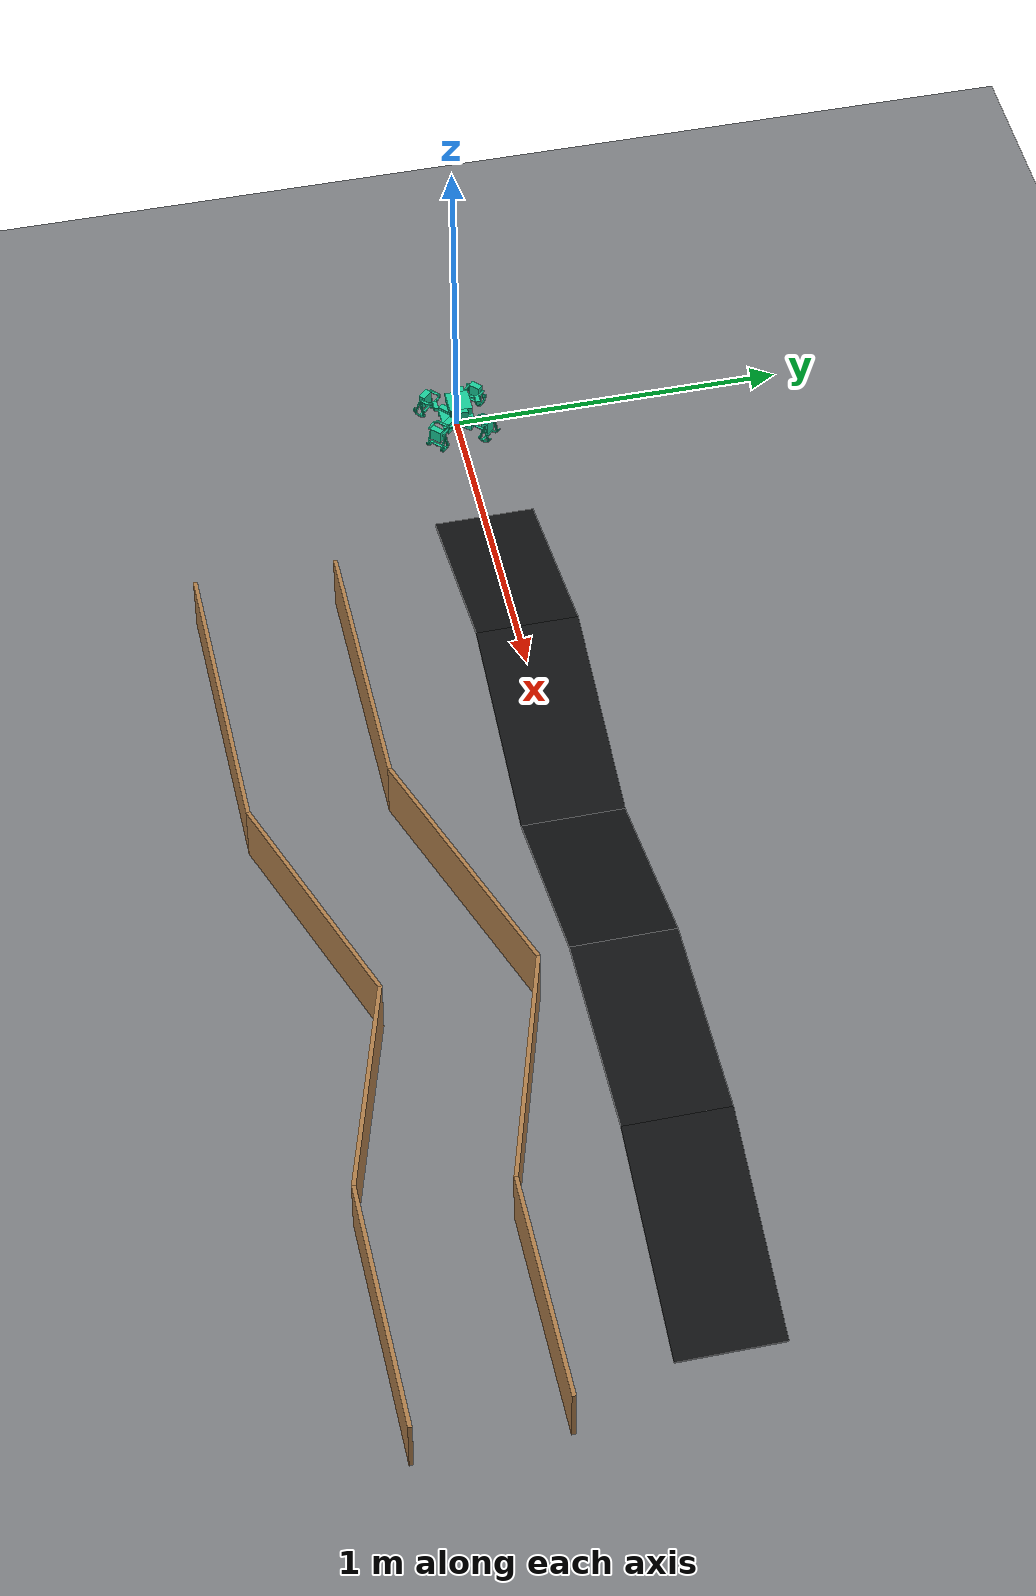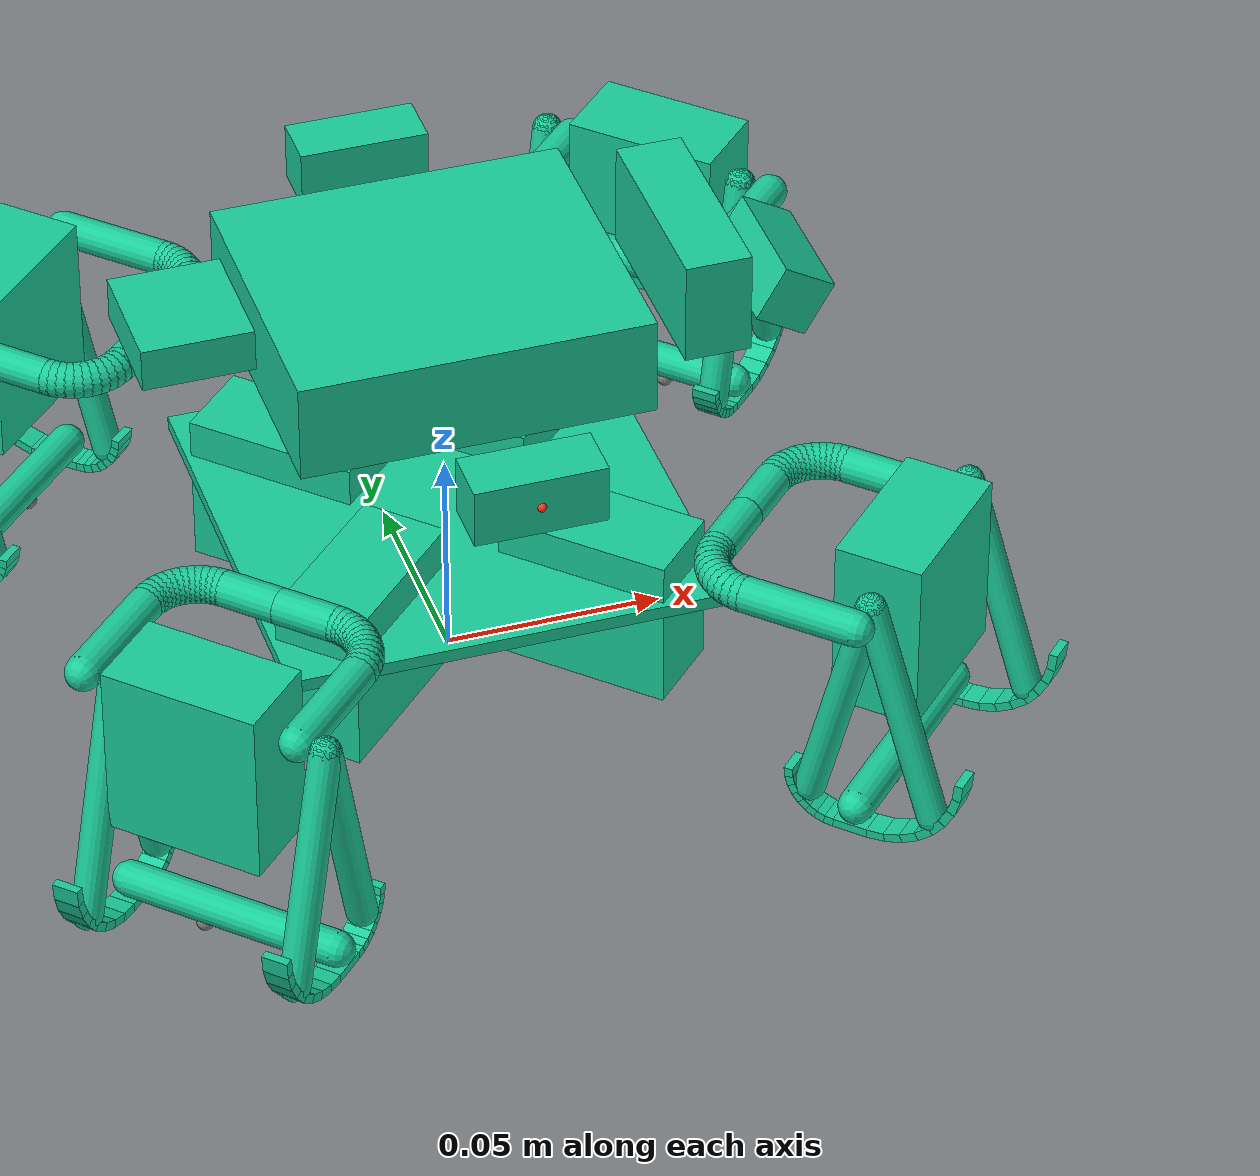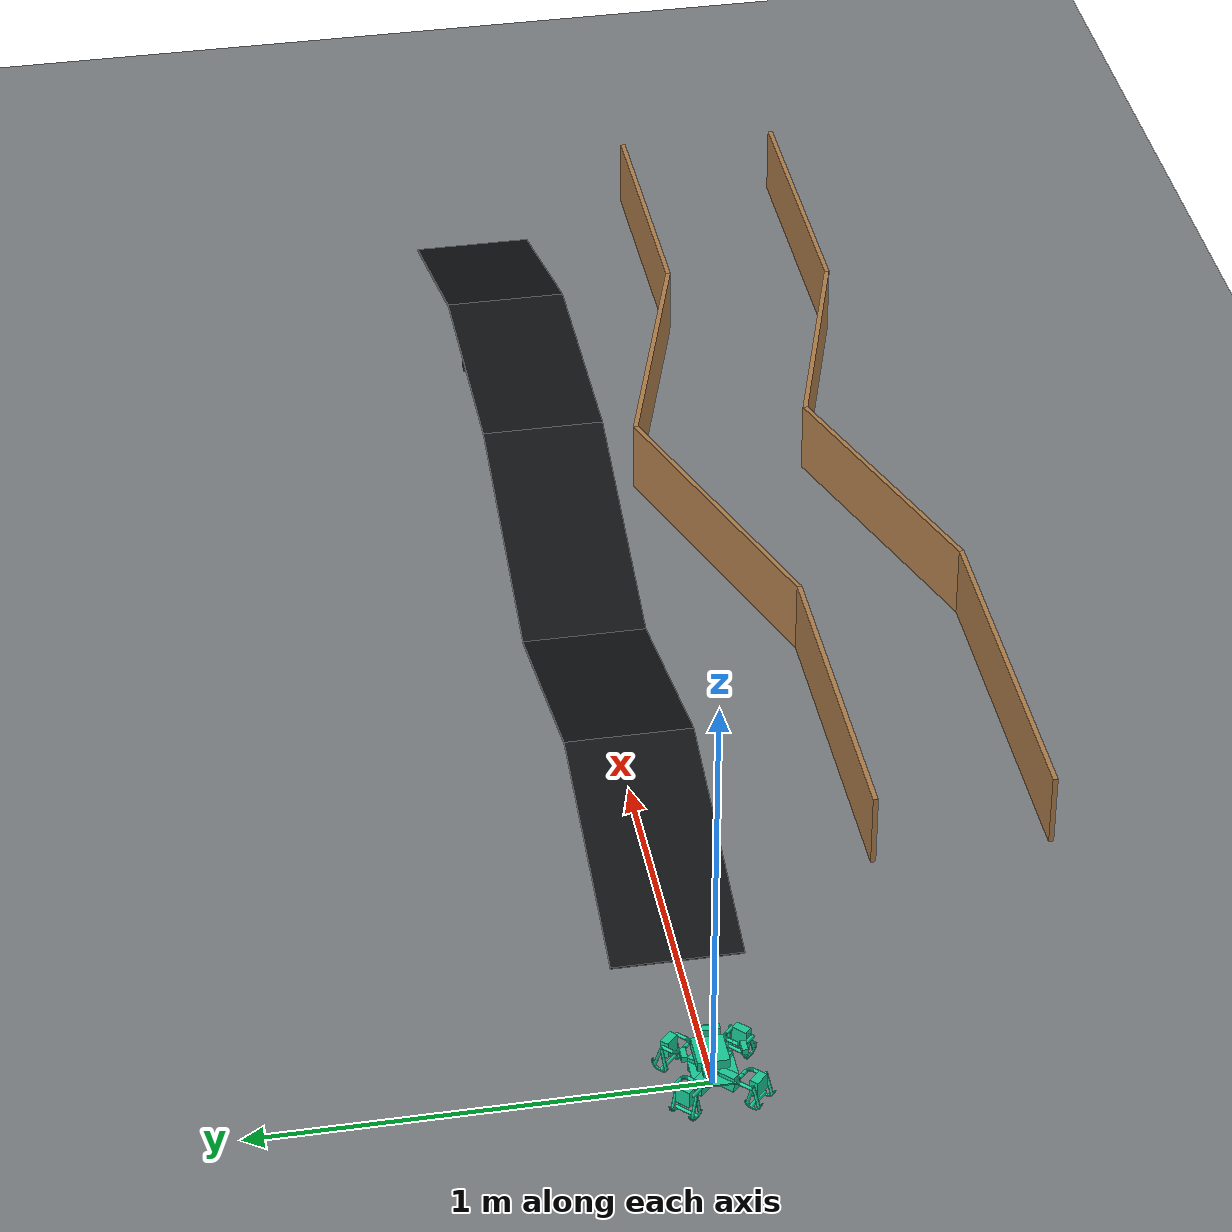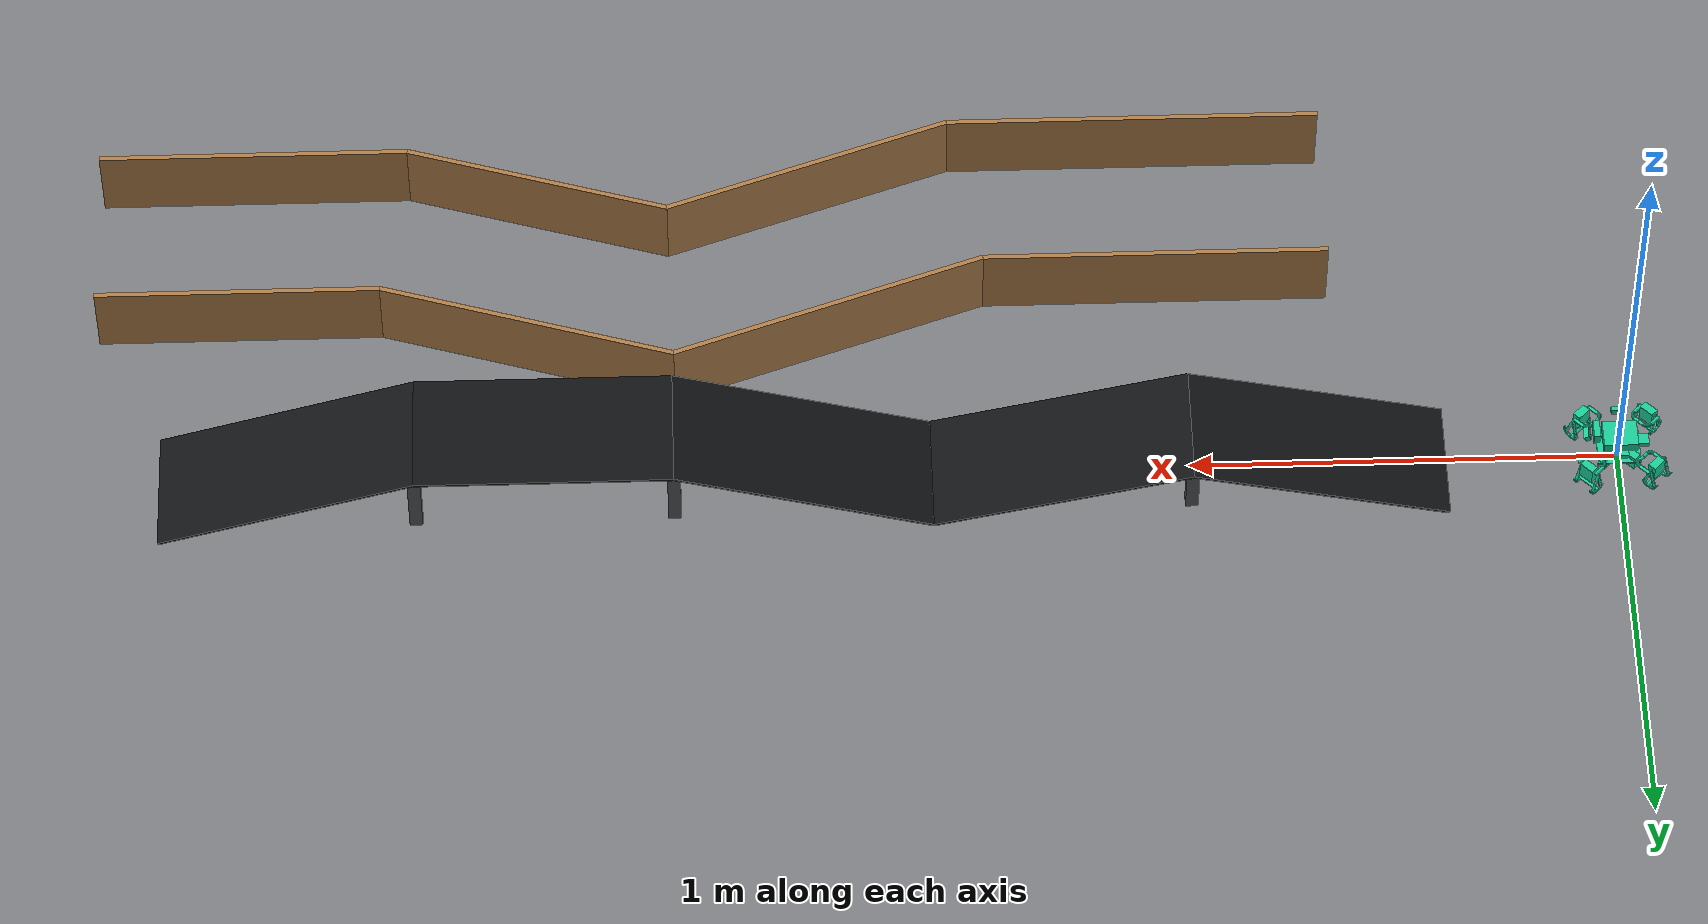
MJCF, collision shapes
<?xml version='1.0' encoding='utf-8'?>
<mujoco model="Design B3 compact rockers">
  <compiler angle="radian" meshdir="robot_meshes_b3" inertiafromgeom="false" autolimits="true" />
  <option timestep=".002" integrator="implicitfast" cone="elliptic" iterations="60" magnetic="0.2 0 -0.45" />
  <visual>
    <global offwidth="1280" offheight="900" />
    <headlight ambient=".45 .45 .45" />
  </visual>
  <asset>
    <texture name="checker" type="2d" builtin="checker" rgb1=".85 .85 .85" rgb2=".12 .14 .17" width="512" height="512" />
    <material name="checker_floor" texture="checker" texrepeat="5 5" texuniform="true" reflectance="0" />
    <mesh name="cad_0" file="cad_0.obj" inertia="shell" maxhullvert="32" />
    <mesh name="cad_1" file="cad_1.obj" inertia="shell" maxhullvert="32" />
    <mesh name="cad_2" file="cad_2.obj" inertia="shell" maxhullvert="32" />
    <mesh name="cad_3" file="cad_3.obj" inertia="shell" maxhullvert="32" />
    <mesh name="cad_4" file="cad_4.obj" inertia="shell" maxhullvert="32" />
    <mesh name="cad_5" file="cad_5.obj" inertia="shell" maxhullvert="32" />
    <mesh name="cad_6" file="cad_6.obj" inertia="shell" maxhullvert="32" />
    <mesh name="cad_7" file="cad_7.obj" inertia="shell" maxhullvert="32" />
    <mesh name="cad_8" file="cad_8.obj" inertia="shell" maxhullvert="32" />
    <mesh name="cad_9" file="cad_9.obj" inertia="shell" maxhullvert="32" />
    <mesh name="cad_10" file="cad_10.obj" inertia="shell" maxhullvert="32" />
    <mesh name="cad_11" file="cad_11.obj" inertia="shell" maxhullvert="32" />
    <mesh name="cad_12" file="cad_12.obj" inertia="shell" maxhullvert="32" />
    <mesh name="cad_13" file="cad_13.obj" inertia="shell" maxhullvert="32" />
    <mesh name="cad_14" file="cad_14.obj" inertia="shell" maxhullvert="32" />
    <mesh name="cad_16" file="cad_16.obj" inertia="shell" maxhullvert="32" />
    <mesh name="cad_17" file="cad_17.obj" inertia="shell" maxhullvert="32" />
    <mesh name="cad_26" file="cad_26.obj" inertia="shell" maxhullvert="32" />
    <mesh name="cad_28" file="cad_28.obj" inertia="shell" maxhullvert="32" />
    <mesh name="cad_29" file="cad_29.obj" inertia="shell" maxhullvert="32" />
    <mesh name="cad_38" file="cad_38.obj" inertia="shell" maxhullvert="32" />
    <mesh name="cad_40" file="cad_40.obj" inertia="shell" maxhullvert="32" />
    <mesh name="cad_41" file="cad_41.obj" inertia="shell" maxhullvert="32" />
    <mesh name="cad_50" file="cad_50.obj" inertia="shell" maxhullvert="32" />
    <mesh name="cad_52" file="cad_52.obj" inertia="shell" maxhullvert="32" />
    <mesh name="cad_53" file="cad_53.obj" inertia="shell" maxhullvert="32" />
    <mesh name="cad_15" file="cad_15.obj" inertia="shell" maxhullvert="32" />
    <mesh name="cad_18" file="cad_18.obj" inertia="shell" maxhullvert="32" />
    <mesh name="cad_20" file="cad_20.obj" inertia="shell" maxhullvert="32" />
    <mesh name="cad_22" file="cad_22.obj" inertia="shell" maxhullvert="32" />
    <mesh name="cad_19" file="cad_19.obj" inertia="shell" maxhullvert="32" />
    <mesh name="cad_21" file="cad_21.obj" inertia="shell" maxhullvert="32" />
    <mesh name="cad_23" file="cad_23.obj" inertia="shell" maxhullvert="32" />
    <mesh name="cad_24" file="cad_24.obj" inertia="shell" maxhullvert="32" />
    <mesh name="cad_25" file="cad_25.obj" inertia="shell" maxhullvert="32" />
    <mesh name="cad_27" file="cad_27.obj" inertia="shell" maxhullvert="32" />
    <mesh name="cad_30" file="cad_30.obj" inertia="shell" maxhullvert="32" />
    <mesh name="cad_32" file="cad_32.obj" inertia="shell" maxhullvert="32" />
    <mesh name="cad_34" file="cad_34.obj" inertia="shell" maxhullvert="32" />
    <mesh name="cad_31" file="cad_31.obj" inertia="shell" maxhullvert="32" />
    <mesh name="cad_33" file="cad_33.obj" inertia="shell" maxhullvert="32" />
    <mesh name="cad_35" file="cad_35.obj" inertia="shell" maxhullvert="32" />
    <mesh name="cad_36" file="cad_36.obj" inertia="shell" maxhullvert="32" />
    <mesh name="cad_37" file="cad_37.obj" inertia="shell" maxhullvert="32" />
    <mesh name="cad_39" file="cad_39.obj" inertia="shell" maxhullvert="32" />
    <mesh name="cad_42" file="cad_42.obj" inertia="shell" maxhullvert="32" />
    <mesh name="cad_44" file="cad_44.obj" inertia="shell" maxhullvert="32" />
    <mesh name="cad_46" file="cad_46.obj" inertia="shell" maxhullvert="32" />
    <mesh name="cad_43" file="cad_43.obj" inertia="shell" maxhullvert="32" />
    <mesh name="cad_45" file="cad_45.obj" inertia="shell" maxhullvert="32" />
    <mesh name="cad_47" file="cad_47.obj" inertia="shell" maxhullvert="32" />
    <mesh name="cad_48" file="cad_48.obj" inertia="shell" maxhullvert="32" />
    <mesh name="cad_49" file="cad_49.obj" inertia="shell" maxhullvert="32" />
    <mesh name="cad_51" file="cad_51.obj" inertia="shell" maxhullvert="32" />
    <mesh name="cad_54" file="cad_54.obj" inertia="shell" maxhullvert="32" />
    <mesh name="cad_56" file="cad_56.obj" inertia="shell" maxhullvert="32" />
    <mesh name="cad_58" file="cad_58.obj" inertia="shell" maxhullvert="32" />
    <mesh name="cad_55" file="cad_55.obj" inertia="shell" maxhullvert="32" />
    <mesh name="cad_57" file="cad_57.obj" inertia="shell" maxhullvert="32" />
    <mesh name="cad_59" file="cad_59.obj" inertia="shell" maxhullvert="32" />
    <mesh name="cad_60" file="cad_60.obj" inertia="shell" maxhullvert="32" />
    <mesh name="cad_61" file="cad_61.obj" inertia="shell" maxhullvert="32" />
    <mesh name="FL_tread_0_0" vertex="0.00353553391 -0.0261629509 -0.048 -0.000707106781 -0.0219203102 -0.048 0.00212132034 -0.0275771645 -0.048 -0.00212132034 -0.0233345238 -0.048 0.00367140249 -0.0260270823 -0.0499509032 -0.000571238196 -0.0217844416 -0.0499509032 0.00228436265 -0.0274141222 -0.0503410839 -0.00195827804 -0.0231714815 -0.0503410839" />
    <mesh name="FL_tread_0_1" vertex="0.00367140249 -0.0260270823 -0.0499509032 -0.000571238196 -0.0217844416 -0.0499509032 0.00228436265 -0.0274141222 -0.0503410839 -0.00195827804 -0.0231714815 -0.0503410839 0.00407378689 -0.0256246979 -0.0518268343 -0.000168853794 -0.0213820572 -0.0518268343 0.00276722393 -0.0269312609 -0.0525922012 -0.00147541676 -0.0226886202 -0.0525922012" />
    <mesh name="FL_tread_0_2" vertex="0.00407378689 -0.0256246979 -0.0518268343 -0.000168853794 -0.0213820572 -0.0518268343 0.00276722393 -0.0269312609 -0.0525922012 -0.00147541676 -0.0226886202 -0.0525922012 0.00472722371 -0.0249712611 -0.0535557023 0.000484583019 -0.0207286204 -0.0535557023 0.0035513481 -0.0261471367 -0.0546668428 -0.000691292584 -0.021904496 -0.0546668428" />
    <mesh name="FL_tread_0_3" vertex="0.00472722371 -0.0249712611 -0.0535557023 0.000484583019 -0.0207286204 -0.0535557023 0.0035513481 -0.0261471367 -0.0546668428 -0.000691292584 -0.021904496 -0.0546668428 0.00560660172 -0.0240918831 -0.0550710678 0.00136396103 -0.0198492424 -0.0550710678 0.00460660172 -0.0250918831 -0.0564852814 0.000363961031 -0.0208492424 -0.0564852814" />
    <mesh name="FL_tread_0_4" vertex="0.00560660172 -0.0240918831 -0.0550710678 0.00136396103 -0.0198492424 -0.0550710678 0.00460660172 -0.0250918831 -0.0564852814 0.000363961031 -0.0208492424 -0.0564852814 0.00667812693 -0.0230203579 -0.0563146961 0.00243548624 -0.0187777172 -0.0563146961 0.00589243197 -0.0238060528 -0.0579776353 0.00164979128 -0.0195634122 -0.0579776353" />
    <mesh name="FL_tread_0_5" vertex="0.00667812693 -0.0230203579 -0.0563146961 0.00243548624 -0.0187777172 -0.0563146961 0.00589243197 -0.0238060528 -0.0579776353 0.00164979128 -0.0195634122 -0.0579776353 0.00790062122 -0.0217978636 -0.0572387953 0.00365798053 -0.0175552229 -0.0572387953 0.00735942512 -0.0223390597 -0.0590865544 0.00311678443 -0.018096419 -0.0590865544" />
    <mesh name="FL_tread_0_6" vertex="0.00790062122 -0.0217978636 -0.0572387953 0.00365798053 -0.0175552229 -0.0572387953 0.00735942512 -0.0223390597 -0.0590865544 0.00311678443 -0.018096419 -0.0590865544 0.00922710482 -0.02047138 -0.0578078528 0.00498446413 -0.0162287393 -0.0578078528 0.00895120544 -0.0207472794 -0.0597694234 0.00470856475 -0.0165046387 -0.0597694234" />
    <mesh name="FL_tread_0_7" vertex="0.00922710482 -0.02047138 -0.0578078528 0.00498446413 -0.0162287393 -0.0578078528 0.00895120544 -0.0207472794 -0.0597694234 0.00470856475 -0.0165046387 -0.0597694234 0.0106066017 -0.0190918831 -0.058 0.00636396103 -0.0148492424 -0.058 0.0106066017 -0.0190918831 -0.06 0.00636396103 -0.0148492424 -0.06" />
    <mesh name="FL_tread_0_8" vertex="0.0106066017 -0.0190918831 -0.058 0.00636396103 -0.0148492424 -0.058 0.0106066017 -0.0190918831 -0.06 0.00636396103 -0.0148492424 -0.06 0.016263456 -0.0134350288 -0.058 0.0120208153 -0.00919238816 -0.058 0.016263456 -0.0134350288 -0.06 0.0120208153 -0.00919238816 -0.06" />
    <mesh name="FL_tread_0_9" vertex="0.016263456 -0.0134350288 -0.058 0.0120208153 -0.00919238816 -0.058 0.016263456 -0.0134350288 -0.06 0.0120208153 -0.00919238816 -0.06 0.0190224498 -0.010676035 -0.0576157056 0.0147798091 -0.00643339436 -0.0576157056 0.0192983491 -0.0104001357 -0.0595772762 0.0150557085 -0.00615749498 -0.0595772762" />
    <mesh name="FL_tread_0_10" vertex="0.0190224498 -0.010676035 -0.0576157056 0.0147798091 -0.00643339436 -0.0576157056 0.0192983491 -0.0104001357 -0.0595772762 0.0150557085 -0.00615749498 -0.0595772762 0.021675417 -0.00802306784 -0.0564775907 0.0174327763 -0.00378042715 -0.0564775907 0.0222166131 -0.00748187174 -0.0583253497 0.0179739724 -0.00323923105 -0.0583253497" />
    <mesh name="FL_tread_0_11" vertex="0.021675417 -0.00802306784 -0.0564775907 0.0174327763 -0.00378042715 -0.0564775907 0.0222166131 -0.00748187174 -0.0583253497 0.0179739724 -0.00323923105 -0.0583253497 0.0241204056 -0.00557807926 -0.0546293922 0.0198777649 -0.00133543857 -0.0546293922 0.0249061005 -0.0047923843 -0.0562923315 0.0206634598 -0.000549743613 -0.0562923315" />
    <mesh name="FL_tread_0_12" vertex="0.0241204056 -0.00557807926 -0.0546293922 0.0198777649 -0.00133543857 -0.0546293922 0.0249061005 -0.0047923843 -0.0562923315 0.0206634598 -0.000549743613 -0.0562923315 0.026263456 -0.00343502884 -0.0521421356 0.0220208153 0.000807611845 -0.0521421356 0.027263456 -0.00243502884 -0.0535563492 0.0230208153 0.00180761184 -0.0535563492" />
    <mesh name="FL_tread_0_13" vertex="0.026263456 -0.00343502884 -0.0521421356 0.0220208153 0.000807611845 -0.0521421356 0.027263456 -0.00243502884 -0.0535563492 0.0230208153 0.00180761184 -0.0535563492 0.028022212 -0.00167627282 -0.0491114047 0.0237795713 0.00256636787 -0.0491114047 0.0291980876 -0.000500397216 -0.0502225451 0.0249554469 0.00374224347 -0.0502225451" />
    <mesh name="FL_tread_0_14" vertex="0.028022212 -0.00167627282 -0.0491114047 0.0237795713 0.00256636787 -0.0491114047 0.0291980876 -0.000500397216 -0.0502225451 0.0249554469 0.00374224347 -0.0502225451 0.0293290856 -0.000369399194 -0.0456536686 0.0250864449 0.00387324149 -0.0456536686 0.0306356486 0.000937163771 -0.0464190355 0.0263930079 0.00517980446 -0.0464190355" />
    <mesh name="FL_tread_0_15" vertex="0.0293290856 -0.000369399194 -0.0456536686 0.0250864449 0.00387324149 -0.0456536686 0.0306356486 0.000937163771 -0.0464190355 0.0263930079 0.00517980446 -0.0464190355 0.0301338544 0.000435369611 -0.0419018064 0.0258912137 0.0046780103 -0.0419018064 0.0315208943 0.00182240946 -0.0422919871 0.0272782536 0.00606505014 -0.0422919871" />
    <mesh name="FL_tread_0_16" vertex="0.0301338544 0.000435369611 -0.0419018064 0.0258912137 0.0046780103 -0.0419018064 0.0315208943 0.00182240946 -0.0422919871 0.0272782536 0.00606505014 -0.0422919871 0.0304055916 0.000707106781 -0.038 0.0261629509 0.00494974747 -0.038 0.0318198052 0.00212132034 -0.038 0.0275771645 0.00636396103 -0.038" />
    <mesh name="FL_tread_1_0" vertex="-0.0318198052 0.00919238816 -0.048 -0.0360624458 0.0134350288 -0.048 -0.0332340187 0.00777817459 -0.048 -0.0374766594 0.0120208153 -0.048 -0.0316839366 0.00932825674 -0.0499509032 -0.0359265773 0.0135708974 -0.0499509032 -0.0330709764 0.0079412169 -0.0503410839 -0.0373136171 0.0121838576 -0.0503410839" />
    <mesh name="FL_tread_1_1" vertex="-0.0316839366 0.00932825674 -0.0499509032 -0.0359265773 0.0135708974 -0.0499509032 -0.0330709764 0.0079412169 -0.0503410839 -0.0373136171 0.0121838576 -0.0503410839 -0.0312815522 0.00973064114 -0.0518268343 -0.0355241929 0.0139732818 -0.0518268343 -0.0325881151 0.00842407818 -0.0525922012 -0.0368307558 0.0126667189 -0.0525922012" />
    <mesh name="FL_tread_1_2" vertex="-0.0312815522 0.00973064114 -0.0518268343 -0.0355241929 0.0139732818 -0.0518268343 -0.0325881151 0.00842407818 -0.0525922012 -0.0368307558 0.0126667189 -0.0525922012 -0.0306281154 0.010384078 -0.0535557023 -0.034870756 0.0146267186 -0.0535557023 -0.031803991 0.00920820235 -0.0546668428 -0.0360466316 0.013450843 -0.0546668428" />
    <mesh name="FL_tread_1_3" vertex="-0.0306281154 0.010384078 -0.0535557023 -0.034870756 0.0146267186 -0.0535557023 -0.031803991 0.00920820235 -0.0546668428 -0.0360466316 0.013450843 -0.0546668428 -0.0297487373 0.011263456 -0.0550710678 -0.033991378 0.0155060967 -0.0550710678 -0.0307487373 0.010263456 -0.0564852814 -0.034991378 0.0145060967 -0.0564852814" />
    <mesh name="FL_tread_1_4" vertex="-0.0297487373 0.011263456 -0.0550710678 -0.033991378 0.0155060967 -0.0550710678 -0.0307487373 0.010263456 -0.0564852814 -0.034991378 0.0145060967 -0.0564852814 -0.0286772121 0.0123349812 -0.0563146961 -0.0329198528 0.0165776219 -0.0563146961 -0.0294629071 0.0115492862 -0.0579776353 -0.0337055478 0.0157919269 -0.0579776353" />
    <mesh name="FL_tread_1_5" vertex="-0.0286772121 0.0123349812 -0.0563146961 -0.0329198528 0.0165776219 -0.0563146961 -0.0294629071 0.0115492862 -0.0579776353 -0.0337055478 0.0157919269 -0.0579776353 -0.0274547178 0.0135574755 -0.0572387953 -0.0316973585 0.0178001162 -0.0572387953 -0.0279959139 0.0130162794 -0.0590865544 -0.0322385546 0.0172589201 -0.0590865544" />
    <mesh name="FL_tread_1_6" vertex="-0.0274547178 0.0135574755 -0.0572387953 -0.0316973585 0.0178001162 -0.0572387953 -0.0279959139 0.0130162794 -0.0590865544 -0.0322385546 0.0172589201 -0.0590865544 -0.0261282342 0.0148839591 -0.0578078528 -0.0303708749 0.0191265998 -0.0578078528 -0.0264041336 0.0146080597 -0.0597694234 -0.0306467743 0.0188507004 -0.0597694234" />
    <mesh name="FL_tread_1_7" vertex="-0.0261282342 0.0148839591 -0.0578078528 -0.0303708749 0.0191265998 -0.0578078528 -0.0264041336 0.0146080597 -0.0597694234 -0.0306467743 0.0188507004 -0.0597694234 -0.0247487373 0.016263456 -0.058 -0.028991378 0.0205060967 -0.058 -0.0247487373 0.016263456 -0.06 -0.028991378 0.0205060967 -0.06" />
    <mesh name="FL_tread_1_8" vertex="-0.0247487373 0.016263456 -0.058 -0.028991378 0.0205060967 -0.058 -0.0247487373 0.016263456 -0.06 -0.028991378 0.0205060967 -0.06 -0.0190918831 0.0219203102 -0.058 -0.0233345238 0.0261629509 -0.058 -0.0190918831 0.0219203102 -0.06 -0.0233345238 0.0261629509 -0.06" />
    <mesh name="FL_tread_1_9" vertex="-0.0190918831 0.0219203102 -0.058 -0.0233345238 0.0261629509 -0.058 -0.0190918831 0.0219203102 -0.06 -0.0233345238 0.0261629509 -0.06 -0.0163328893 0.024679304 -0.0576157056 -0.02057553 0.0289219447 -0.0576157056 -0.0160569899 0.0249552034 -0.0595772762 -0.0202996306 0.0291978441 -0.0595772762" />
    <mesh name="FL_tread_1_10" vertex="-0.0163328893 0.024679304 -0.0576157056 -0.02057553 0.0289219447 -0.0576157056 -0.0160569899 0.0249552034 -0.0595772762 -0.0202996306 0.0291978441 -0.0595772762 -0.0136799221 0.0273322712 -0.0564775907 -0.0179225628 0.0315749119 -0.0564775907 -0.013138726 0.0278734673 -0.0583253497 -0.0173813667 0.032116108 -0.0583253497" />
    <mesh name="FL_tread_1_11" vertex="-0.0136799221 0.0273322712 -0.0564775907 -0.0179225628 0.0315749119 -0.0564775907 -0.013138726 0.0278734673 -0.0583253497 -0.0173813667 0.032116108 -0.0583253497 -0.0112349335 0.0297772598 -0.0546293922 -0.0154775742 0.0340199005 -0.0546293922 -0.0104492385 0.0305629548 -0.0562923315 -0.0146918792 0.0348055954 -0.0562923315" />
    <mesh name="FL_tread_1_12" vertex="-0.0112349335 0.0297772598 -0.0546293922 -0.0154775742 0.0340199005 -0.0546293922 -0.0104492385 0.0305629548 -0.0562923315 -0.0146918792 0.0348055954 -0.0562923315 -0.00909188309 0.0319203102 -0.0521421356 -0.0133345238 0.0361629509 -0.0521421356 -0.00809188309 0.0329203102 -0.0535563492 -0.0123345238 0.0371629509 -0.0535563492" />
    <mesh name="FL_tread_1_13" vertex="-0.00909188309 0.0319203102 -0.0521421356 -0.0133345238 0.0361629509 -0.0521421356 -0.00809188309 0.0329203102 -0.0535563492 -0.0123345238 0.0371629509 -0.0535563492 -0.00733312707 0.0336790662 -0.0491114047 -0.0115757678 0.0379217069 -0.0491114047 -0.00615725147 0.0348549418 -0.0502225451 -0.0103998922 0.0390975825 -0.0502225451" />
    <mesh name="FL_tread_1_14" vertex="-0.00733312707 0.0336790662 -0.0491114047 -0.0115757678 0.0379217069 -0.0491114047 -0.00615725147 0.0348549418 -0.0502225451 -0.0103998922 0.0390975825 -0.0502225451 -0.00602625344 0.0349859399 -0.0456536686 -0.0102688941 0.0392285806 -0.0456536686 -0.00471969048 0.0362925028 -0.0464190355 -0.00896233117 0.0405351435 -0.0464190355" />
    <mesh name="FL_tread_1_15" vertex="-0.00602625344 0.0349859399 -0.0456536686 -0.0102688941 0.0392285806 -0.0456536686 -0.00471969048 0.0362925028 -0.0464190355 -0.00896233117 0.0405351435 -0.0464190355 -0.00522148464 0.0357907087 -0.0419018064 -0.00946412533 0.0400333494 -0.0419018064 -0.00383444479 0.0371777485 -0.0422919871 -0.00807708548 0.0414203892 -0.0422919871" />
    <mesh name="FL_tread_1_16" vertex="-0.00522148464 0.0357907087 -0.0419018064 -0.00946412533 0.0400333494 -0.0419018064 -0.00383444479 0.0371777485 -0.0422919871 -0.00807708548 0.0414203892 -0.0422919871 -0.00494974747 0.0360624458 -0.038 -0.00919238816 0.0403050865 -0.038 -0.00353553391 0.0374766594 -0.038 -0.00777817459 0.0417193001 -0.038" />
    <mesh name="RL_tread_0_0" vertex="0.0261629509 0.00353553391 -0.048 0.0219203102 -0.000707106781 -0.048 0.0275771645 0.00212132034 -0.048 0.0233345238 -0.00212132034 -0.048 0.0260270823 0.00367140249 -0.0499509032 0.0217844416 -0.000571238196 -0.0499509032 0.0274141222 0.00228436265 -0.0503410839 0.0231714815 -0.00195827804 -0.0503410839" />
    <mesh name="RL_tread_0_1" vertex="0.0260270823 0.00367140249 -0.0499509032 0.0217844416 -0.000571238196 -0.0499509032 0.0274141222 0.00228436265 -0.0503410839 0.0231714815 -0.00195827804 -0.0503410839 0.0256246979 0.00407378689 -0.0518268343 0.0213820572 -0.000168853794 -0.0518268343 0.0269312609 0.00276722393 -0.0525922012 0.0226886202 -0.00147541676 -0.0525922012" />
    <mesh name="RL_tread_0_2" vertex="0.0256246979 0.00407378689 -0.0518268343 0.0213820572 -0.000168853794 -0.0518268343 0.0269312609 0.00276722393 -0.0525922012 0.0226886202 -0.00147541676 -0.0525922012 0.0249712611 0.00472722371 -0.0535557023 0.0207286204 0.000484583019 -0.0535557023 0.0261471367 0.0035513481 -0.0546668428 0.021904496 -0.000691292584 -0.0546668428" />
    <mesh name="RL_tread_0_3" vertex="0.0249712611 0.00472722371 -0.0535557023 0.0207286204 0.000484583019 -0.0535557023 0.0261471367 0.0035513481 -0.0546668428 0.021904496 -0.000691292584 -0.0546668428 0.0240918831 0.00560660172 -0.0550710678 0.0198492424 0.00136396103 -0.0550710678 0.0250918831 0.00460660172 -0.0564852814 0.0208492424 0.000363961031 -0.0564852814" />
    <mesh name="RL_tread_0_4" vertex="0.0240918831 0.00560660172 -0.0550710678 0.0198492424 0.00136396103 -0.0550710678 0.0250918831 0.00460660172 -0.0564852814 0.0208492424 0.000363961031 -0.0564852814 0.0230203579 0.00667812693 -0.0563146961 0.0187777172 0.00243548624 -0.0563146961 0.0238060528 0.00589243197 -0.0579776353 0.0195634122 0.00164979128 -0.0579776353" />
    <mesh name="RL_tread_0_5" vertex="0.0230203579 0.00667812693 -0.0563146961 0.0187777172 0.00243548624 -0.0563146961 0.0238060528 0.00589243197 -0.0579776353 0.0195634122 0.00164979128 -0.0579776353 0.0217978636 0.00790062122 -0.0572387953 0.0175552229 0.00365798053 -0.0572387953 0.0223390597 0.00735942512 -0.0590865544 0.018096419 0.00311678443 -0.0590865544" />
    <mesh name="RL_tread_0_6" vertex="0.0217978636 0.00790062122 -0.0572387953 0.0175552229 0.00365798053 -0.0572387953 0.0223390597 0.00735942512 -0.0590865544 0.018096419 0.00311678443 -0.0590865544 0.02047138 0.00922710482 -0.0578078528 0.0162287393 0.00498446413 -0.0578078528 0.0207472794 0.00895120544 -0.0597694234 0.0165046387 0.00470856475 -0.0597694234" />
    <mesh name="RL_tread_0_7" vertex="0.02047138 0.00922710482 -0.0578078528 0.0162287393 0.00498446413 -0.0578078528 0.0207472794 0.00895120544 -0.0597694234 0.0165046387 0.00470856475 -0.0597694234 0.0190918831 0.0106066017 -0.058 0.0148492424 0.00636396103 -0.058 0.0190918831 0.0106066017 -0.06 0.0148492424 0.00636396103 -0.06" />
    <mesh name="RL_tread_0_8" vertex="0.0190918831 0.0106066017 -0.058 0.0148492424 0.00636396103 -0.058 0.0190918831 0.0106066017 -0.06 0.0148492424 0.00636396103 -0.06 0.0134350288 0.016263456 -0.058 0.00919238816 0.0120208153 -0.058 0.0134350288 0.016263456 -0.06 0.00919238816 0.0120208153 -0.06" />
    <mesh name="RL_tread_0_9" vertex="0.0134350288 0.016263456 -0.058 0.00919238816 0.0120208153 -0.058 0.0134350288 0.016263456 -0.06 0.00919238816 0.0120208153 -0.06 0.010676035 0.0190224498 -0.0576157056 0.00643339436 0.0147798091 -0.0576157056 0.0104001357 0.0192983491 -0.0595772762 0.00615749498 0.0150557085 -0.0595772762" />
    <mesh name="RL_tread_0_10" vertex="0.010676035 0.0190224498 -0.0576157056 0.00643339436 0.0147798091 -0.0576157056 0.0104001357 0.0192983491 -0.0595772762 0.00615749498 0.0150557085 -0.0595772762 0.00802306784 0.021675417 -0.0564775907 0.00378042715 0.0174327763 -0.0564775907 0.00748187174 0.0222166131 -0.0583253497 0.00323923105 0.0179739724 -0.0583253497" />
    <mesh name="RL_tread_0_11" vertex="0.00802306784 0.021675417 -0.0564775907 0.00378042715 0.0174327763 -0.0564775907 0.00748187174 0.0222166131 -0.0583253497 0.00323923105 0.0179739724 -0.0583253497 0.00557807926 0.0241204056 -0.0546293922 0.00133543857 0.0198777649 -0.0546293922 0.0047923843 0.0249061005 -0.0562923315 0.000549743613 0.0206634598 -0.0562923315" />
    <mesh name="RL_tread_0_12" vertex="0.00557807926 0.0241204056 -0.0546293922 0.00133543857 0.0198777649 -0.0546293922 0.0047923843 0.0249061005 -0.0562923315 0.000549743613 0.0206634598 -0.0562923315 0.00343502884 0.026263456 -0.0521421356 -0.000807611845 0.0220208153 -0.0521421356 0.00243502884 0.027263456 -0.0535563492 -0.00180761184 0.0230208153 -0.0535563492" />
    <mesh name="RL_tread_0_13" vertex="0.00343502884 0.026263456 -0.0521421356 -0.000807611845 0.0220208153 -0.0521421356 0.00243502884 0.027263456 -0.0535563492 -0.00180761184 0.0230208153 -0.0535563492 0.00167627282 0.028022212 -0.0491114047 -0.00256636787 0.0237795713 -0.0491114047 0.000500397216 0.0291980876 -0.0502225451 -0.00374224347 0.0249554469 -0.0502225451" />
    <mesh name="RL_tread_0_14" vertex="0.00167627282 0.028022212 -0.0491114047 -0.00256636787 0.0237795713 -0.0491114047 0.000500397216 0.0291980876 -0.0502225451 -0.00374224347 0.0249554469 -0.0502225451 0.000369399194 0.0293290856 -0.0456536686 -0.00387324149 0.0250864449 -0.0456536686 -0.000937163771 0.0306356486 -0.0464190355 -0.00517980446 0.0263930079 -0.0464190355" />
    <mesh name="RL_tread_0_15" vertex="0.000369399194 0.0293290856 -0.0456536686 -0.00387324149 0.0250864449 -0.0456536686 -0.000937163771 0.0306356486 -0.0464190355 -0.00517980446 0.0263930079 -0.0464190355 -0.000435369611 0.0301338544 -0.0419018064 -0.0046780103 0.0258912137 -0.0419018064 -0.00182240946 0.0315208943 -0.0422919871 -0.00606505014 0.0272782536 -0.0422919871" />
    <mesh name="RL_tread_0_16" vertex="-0.000435369611 0.0301338544 -0.0419018064 -0.0046780103 0.0258912137 -0.0419018064 -0.00182240946 0.0315208943 -0.0422919871 -0.00606505014 0.0272782536 -0.0422919871 -0.000707106781 0.0304055916 -0.038 -0.00494974747 0.0261629509 -0.038 -0.00212132034 0.0318198052 -0.038 -0.00636396103 0.0275771645 -0.038" />
    <mesh name="RL_tread_1_0" vertex="-0.00919238816 -0.0318198052 -0.048 -0.0134350288 -0.0360624458 -0.048 -0.00777817459 -0.0332340187 -0.048 -0.0120208153 -0.0374766594 -0.048 -0.00932825674 -0.0316839366 -0.0499509032 -0.0135708974 -0.0359265773 -0.0499509032 -0.0079412169 -0.0330709764 -0.0503410839 -0.0121838576 -0.0373136171 -0.0503410839" />
    <mesh name="RL_tread_1_1" vertex="-0.00932825674 -0.0316839366 -0.0499509032 -0.0135708974 -0.0359265773 -0.0499509032 -0.0079412169 -0.0330709764 -0.0503410839 -0.0121838576 -0.0373136171 -0.0503410839 -0.00973064114 -0.0312815522 -0.0518268343 -0.0139732818 -0.0355241929 -0.0518268343 -0.00842407818 -0.0325881151 -0.0525922012 -0.0126667189 -0.0368307558 -0.0525922012" />
    <mesh name="RL_tread_1_2" vertex="-0.00973064114 -0.0312815522 -0.0518268343 -0.0139732818 -0.0355241929 -0.0518268343 -0.00842407818 -0.0325881151 -0.0525922012 -0.0126667189 -0.0368307558 -0.0525922012 -0.010384078 -0.0306281154 -0.0535557023 -0.0146267186 -0.034870756 -0.0535557023 -0.00920820235 -0.031803991 -0.0546668428 -0.013450843 -0.0360466316 -0.0546668428" />
    <mesh name="RL_tread_1_3" vertex="-0.010384078 -0.0306281154 -0.0535557023 -0.0146267186 -0.034870756 -0.0535557023 -0.00920820235 -0.031803991 -0.0546668428 -0.013450843 -0.0360466316 -0.0546668428 -0.011263456 -0.0297487373 -0.0550710678 -0.0155060967 -0.033991378 -0.0550710678 -0.010263456 -0.0307487373 -0.0564852814 -0.0145060967 -0.034991378 -0.0564852814" />
    <mesh name="RL_tread_1_4" vertex="-0.011263456 -0.0297487373 -0.0550710678 -0.0155060967 -0.033991378 -0.0550710678 -0.010263456 -0.0307487373 -0.0564852814 -0.0145060967 -0.034991378 -0.0564852814 -0.0123349812 -0.0286772121 -0.0563146961 -0.0165776219 -0.0329198528 -0.0563146961 -0.0115492862 -0.0294629071 -0.0579776353 -0.0157919269 -0.0337055478 -0.0579776353" />
    <mesh name="RL_tread_1_5" vertex="-0.0123349812 -0.0286772121 -0.0563146961 -0.0165776219 -0.0329198528 -0.0563146961 -0.0115492862 -0.0294629071 -0.0579776353 -0.0157919269 -0.0337055478 -0.0579776353 -0.0135574755 -0.0274547178 -0.0572387953 -0.0178001162 -0.0316973585 -0.0572387953 -0.0130162794 -0.0279959139 -0.0590865544 -0.0172589201 -0.0322385546 -0.0590865544" />
    <mesh name="RL_tread_1_6" vertex="-0.0135574755 -0.0274547178 -0.0572387953 -0.0178001162 -0.0316973585 -0.0572387953 -0.0130162794 -0.0279959139 -0.0590865544 -0.0172589201 -0.0322385546 -0.0590865544 -0.0148839591 -0.0261282342 -0.0578078528 -0.0191265998 -0.0303708749 -0.0578078528 -0.0146080597 -0.0264041336 -0.0597694234 -0.0188507004 -0.0306467743 -0.0597694234" />
    <mesh name="RL_tread_1_7" vertex="-0.0148839591 -0.0261282342 -0.0578078528 -0.0191265998 -0.0303708749 -0.0578078528 -0.0146080597 -0.0264041336 -0.0597694234 -0.0188507004 -0.0306467743 -0.0597694234 -0.016263456 -0.0247487373 -0.058 -0.0205060967 -0.028991378 -0.058 -0.016263456 -0.0247487373 -0.06 -0.0205060967 -0.028991378 -0.06" />
    <mesh name="RL_tread_1_8" vertex="-0.016263456 -0.0247487373 -0.058 -0.0205060967 -0.028991378 -0.058 -0.016263456 -0.0247487373 -0.06 -0.0205060967 -0.028991378 -0.06 -0.0219203102 -0.0190918831 -0.058 -0.0261629509 -0.0233345238 -0.058 -0.0219203102 -0.0190918831 -0.06 -0.0261629509 -0.0233345238 -0.06" />
    <mesh name="RL_tread_1_9" vertex="-0.0219203102 -0.0190918831 -0.058 -0.0261629509 -0.0233345238 -0.058 -0.0219203102 -0.0190918831 -0.06 -0.0261629509 -0.0233345238 -0.06 -0.024679304 -0.0163328893 -0.0576157056 -0.0289219447 -0.02057553 -0.0576157056 -0.0249552034 -0.0160569899 -0.0595772762 -0.0291978441 -0.0202996306 -0.0595772762" />
    <mesh name="RL_tread_1_10" vertex="-0.024679304 -0.0163328893 -0.0576157056 -0.0289219447 -0.02057553 -0.0576157056 -0.0249552034 -0.0160569899 -0.0595772762 -0.0291978441 -0.0202996306 -0.0595772762 -0.0273322712 -0.0136799221 -0.0564775907 -0.0315749119 -0.0179225628 -0.0564775907 -0.0278734673 -0.013138726 -0.0583253497 -0.032116108 -0.0173813667 -0.0583253497" />
    <mesh name="RL_tread_1_11" vertex="-0.0273322712 -0.0136799221 -0.0564775907 -0.0315749119 -0.0179225628 -0.0564775907 -0.0278734673 -0.013138726 -0.0583253497 -0.032116108 -0.0173813667 -0.0583253497 -0.0297772598 -0.0112349335 -0.0546293922 -0.0340199005 -0.0154775742 -0.0546293922 -0.0305629548 -0.0104492385 -0.0562923315 -0.0348055954 -0.0146918792 -0.0562923315" />
    <mesh name="RL_tread_1_12" vertex="-0.0297772598 -0.0112349335 -0.0546293922 -0.0340199005 -0.0154775742 -0.0546293922 -0.0305629548 -0.0104492385 -0.0562923315 -0.0348055954 -0.0146918792 -0.0562923315 -0.0319203102 -0.00909188309 -0.0521421356 -0.0361629509 -0.0133345238 -0.0521421356 -0.0329203102 -0.00809188309 -0.0535563492 -0.0371629509 -0.0123345238 -0.0535563492" />
    <mesh name="RL_tread_1_13" vertex="-0.0319203102 -0.00909188309 -0.0521421356 -0.0361629509 -0.0133345238 -0.0521421356 -0.0329203102 -0.00809188309 -0.0535563492 -0.0371629509 -0.0123345238 -0.0535563492 -0.0336790662 -0.00733312707 -0.0491114047 -0.0379217069 -0.0115757678 -0.0491114047 -0.0348549418 -0.00615725147 -0.0502225451 -0.0390975825 -0.0103998922 -0.0502225451" />
    <mesh name="RL_tread_1_14" vertex="-0.0336790662 -0.00733312707 -0.0491114047 -0.0379217069 -0.0115757678 -0.0491114047 -0.0348549418 -0.00615725147 -0.0502225451 -0.0390975825 -0.0103998922 -0.0502225451 -0.0349859399 -0.00602625344 -0.0456536686 -0.0392285806 -0.0102688941 -0.0456536686 -0.0362925028 -0.00471969048 -0.0464190355 -0.0405351435 -0.00896233117 -0.0464190355" />
    <mesh name="RL_tread_1_15" vertex="-0.0349859399 -0.00602625344 -0.0456536686 -0.0392285806 -0.0102688941 -0.0456536686 -0.0362925028 -0.00471969048 -0.0464190355 -0.0405351435 -0.00896233117 -0.0464190355 -0.0357907087 -0.00522148464 -0.0419018064 -0.0400333494 -0.00946412533 -0.0419018064 -0.0371777485 -0.00383444479 -0.0422919871 -0.0414203892 -0.00807708548 -0.0422919871" />
    <mesh name="RL_tread_1_16" vertex="-0.0357907087 -0.00522148464 -0.0419018064 -0.0400333494 -0.00946412533 -0.0419018064 -0.0371777485 -0.00383444479 -0.0422919871 -0.0414203892 -0.00807708548 -0.0422919871 -0.0360624458 -0.00494974747 -0.038 -0.0403050865 -0.00919238816 -0.038 -0.0374766594 -0.00353553391 -0.038 -0.0417193001 -0.00777817459 -0.038" />
    <mesh name="FR_tread_0_0" vertex="-0.0261629509 -0.00353553391 -0.048 -0.0219203102 0.000707106781 -0.048 -0.0275771645 -0.00212132034 -0.048 -0.0233345238 0.00212132034 -0.048 -0.0260270823 -0.00367140249 -0.0499509032 -0.0217844416 0.000571238196 -0.0499509032 -0.0274141222 -0.00228436265 -0.0503410839 -0.0231714815 0.00195827804 -0.0503410839" />
    <mesh name="FR_tread_0_1" vertex="-0.0260270823 -0.00367140249 -0.0499509032 -0.0217844416 0.000571238196 -0.0499509032 -0.0274141222 -0.00228436265 -0.0503410839 -0.0231714815 0.00195827804 -0.0503410839 -0.0256246979 -0.00407378689 -0.0518268343 -0.0213820572 0.000168853794 -0.0518268343 -0.0269312609 -0.00276722393 -0.0525922012 -0.0226886202 0.00147541676 -0.0525922012" />
    <mesh name="FR_tread_0_2" vertex="-0.0256246979 -0.00407378689 -0.0518268343 -0.0213820572 0.000168853794 -0.0518268343 -0.0269312609 -0.00276722393 -0.0525922012 -0.0226886202 0.00147541676 -0.0525922012 -0.0249712611 -0.00472722371 -0.0535557023 -0.0207286204 -0.000484583019 -0.0535557023 -0.0261471367 -0.0035513481 -0.0546668428 -0.021904496 0.000691292584 -0.0546668428" />
    <mesh name="FR_tread_0_3" vertex="-0.0249712611 -0.00472722371 -0.0535557023 -0.0207286204 -0.000484583019 -0.0535557023 -0.0261471367 -0.0035513481 -0.0546668428 -0.021904496 0.000691292584 -0.0546668428 -0.0240918831 -0.00560660172 -0.0550710678 -0.0198492424 -0.00136396103 -0.0550710678 -0.0250918831 -0.00460660172 -0.0564852814 -0.0208492424 -0.000363961031 -0.0564852814" />
    <mesh name="FR_tread_0_4" vertex="-0.0240918831 -0.00560660172 -0.0550710678 -0.0198492424 -0.00136396103 -0.0550710678 -0.0250918831 -0.00460660172 -0.0564852814 -0.0208492424 -0.000363961031 -0.0564852814 -0.0230203579 -0.00667812693 -0.0563146961 -0.0187777172 -0.00243548624 -0.0563146961 -0.0238060528 -0.00589243197 -0.0579776353 -0.0195634122 -0.00164979128 -0.0579776353" />
    <mesh name="FR_tread_0_5" vertex="-0.0230203579 -0.00667812693 -0.0563146961 -0.0187777172 -0.00243548624 -0.0563146961 -0.0238060528 -0.00589243197 -0.0579776353 -0.0195634122 -0.00164979128 -0.0579776353 -0.0217978636 -0.00790062122 -0.0572387953 -0.0175552229 -0.00365798053 -0.0572387953 -0.0223390597 -0.00735942512 -0.0590865544 -0.018096419 -0.00311678443 -0.0590865544" />
    <mesh name="FR_tread_0_6" vertex="-0.0217978636 -0.00790062122 -0.0572387953 -0.0175552229 -0.00365798053 -0.0572387953 -0.0223390597 -0.00735942512 -0.0590865544 -0.018096419 -0.00311678443 -0.0590865544 -0.02047138 -0.00922710482 -0.0578078528 -0.0162287393 -0.00498446413 -0.0578078528 -0.0207472794 -0.00895120544 -0.0597694234 -0.0165046387 -0.00470856475 -0.0597694234" />
    <mesh name="FR_tread_0_7" vertex="-0.02047138 -0.00922710482 -0.0578078528 -0.0162287393 -0.00498446413 -0.0578078528 -0.0207472794 -0.00895120544 -0.0597694234 -0.0165046387 -0.00470856475 -0.0597694234 -0.0190918831 -0.0106066017 -0.058 -0.0148492424 -0.00636396103 -0.058 -0.0190918831 -0.0106066017 -0.06 -0.0148492424 -0.00636396103 -0.06" />
    <mesh name="FR_tread_0_8" vertex="-0.0190918831 -0.0106066017 -0.058 -0.0148492424 -0.00636396103 -0.058 -0.0190918831 -0.0106066017 -0.06 -0.0148492424 -0.00636396103 -0.06 -0.0134350288 -0.016263456 -0.058 -0.00919238816 -0.0120208153 -0.058 -0.0134350288 -0.016263456 -0.06 -0.00919238816 -0.0120208153 -0.06" />
    <mesh name="FR_tread_0_9" vertex="-0.0134350288 -0.016263456 -0.058 -0.00919238816 -0.0120208153 -0.058 -0.0134350288 -0.016263456 -0.06 -0.00919238816 -0.0120208153 -0.06 -0.010676035 -0.0190224498 -0.0576157056 -0.00643339436 -0.0147798091 -0.0576157056 -0.0104001357 -0.0192983491 -0.0595772762 -0.00615749498 -0.0150557085 -0.0595772762" />
    <mesh name="FR_tread_0_10" vertex="-0.010676035 -0.0190224498 -0.0576157056 -0.00643339436 -0.0147798091 -0.0576157056 -0.0104001357 -0.0192983491 -0.0595772762 -0.00615749498 -0.0150557085 -0.0595772762 -0.00802306784 -0.021675417 -0.0564775907 -0.00378042715 -0.0174327763 -0.0564775907 -0.00748187174 -0.0222166131 -0.0583253497 -0.00323923105 -0.0179739724 -0.0583253497" />
    <mesh name="FR_tread_0_11" vertex="-0.00802306784 -0.021675417 -0.0564775907 -0.00378042715 -0.0174327763 -0.0564775907 -0.00748187174 -0.0222166131 -0.0583253497 -0.00323923105 -0.0179739724 -0.0583253497 -0.00557807926 -0.0241204056 -0.0546293922 -0.00133543857 -0.0198777649 -0.0546293922 -0.0047923843 -0.0249061005 -0.0562923315 -0.000549743613 -0.0206634598 -0.0562923315" />
    <mesh name="FR_tread_0_12" vertex="-0.00557807926 -0.0241204056 -0.0546293922 -0.00133543857 -0.0198777649 -0.0546293922 -0.0047923843 -0.0249061005 -0.0562923315 -0.000549743613 -0.0206634598 -0.0562923315 -0.00343502884 -0.026263456 -0.0521421356 0.000807611845 -0.0220208153 -0.0521421356 -0.00243502884 -0.027263456 -0.0535563492 0.00180761184 -0.0230208153 -0.0535563492" />
    <mesh name="FR_tread_0_13" vertex="-0.00343502884 -0.026263456 -0.0521421356 0.000807611845 -0.0220208153 -0.0521421356 -0.00243502884 -0.027263456 -0.0535563492 0.00180761184 -0.0230208153 -0.0535563492 -0.00167627282 -0.028022212 -0.0491114047 0.00256636787 -0.0237795713 -0.0491114047 -0.000500397216 -0.0291980876 -0.0502225451 0.00374224347 -0.0249554469 -0.0502225451" />
    <mesh name="FR_tread_0_14" vertex="-0.00167627282 -0.028022212 -0.0491114047 0.00256636787 -0.0237795713 -0.0491114047 -0.000500397216 -0.0291980876 -0.0502225451 0.00374224347 -0.0249554469 -0.0502225451 -0.000369399194 -0.0293290856 -0.0456536686 0.00387324149 -0.0250864449 -0.0456536686 0.000937163771 -0.0306356486 -0.0464190355 0.00517980446 -0.0263930079 -0.0464190355" />
    <mesh name="FR_tread_0_15" vertex="-0.000369399194 -0.0293290856 -0.0456536686 0.00387324149 -0.0250864449 -0.0456536686 0.000937163771 -0.0306356486 -0.0464190355 0.00517980446 -0.0263930079 -0.0464190355 0.000435369611 -0.0301338544 -0.0419018064 0.0046780103 -0.0258912137 -0.0419018064 0.00182240946 -0.0315208943 -0.0422919871 0.00606505014 -0.0272782536 -0.0422919871" />
    <mesh name="FR_tread_0_16" vertex="0.000435369611 -0.0301338544 -0.0419018064 0.0046780103 -0.0258912137 -0.0419018064 0.00182240946 -0.0315208943 -0.0422919871 0.00606505014 -0.0272782536 -0.0422919871 0.000707106781 -0.0304055916 -0.038 0.00494974747 -0.0261629509 -0.038 0.00212132034 -0.0318198052 -0.038 0.00636396103 -0.0275771645 -0.038" />
    <mesh name="FR_tread_1_0" vertex="0.00919238816 0.0318198052 -0.048 0.0134350288 0.0360624458 -0.048 0.00777817459 0.0332340187 -0.048 0.0120208153 0.0374766594 -0.048 0.00932825674 0.0316839366 -0.0499509032 0.0135708974 0.0359265773 -0.0499509032 0.0079412169 0.0330709764 -0.0503410839 0.0121838576 0.0373136171 -0.0503410839" />
    <mesh name="FR_tread_1_1" vertex="0.00932825674 0.0316839366 -0.0499509032 0.0135708974 0.0359265773 -0.0499509032 0.0079412169 0.0330709764 -0.0503410839 0.0121838576 0.0373136171 -0.0503410839 0.00973064114 0.0312815522 -0.0518268343 0.0139732818 0.0355241929 -0.0518268343 0.00842407818 0.0325881151 -0.0525922012 0.0126667189 0.0368307558 -0.0525922012" />
    <mesh name="FR_tread_1_2" vertex="0.00973064114 0.0312815522 -0.0518268343 0.0139732818 0.0355241929 -0.0518268343 0.00842407818 0.0325881151 -0.0525922012 0.0126667189 0.0368307558 -0.0525922012 0.010384078 0.0306281154 -0.0535557023 0.0146267186 0.034870756 -0.0535557023 0.00920820235 0.031803991 -0.0546668428 0.013450843 0.0360466316 -0.0546668428" />
    <mesh name="FR_tread_1_3" vertex="0.010384078 0.0306281154 -0.0535557023 0.0146267186 0.034870756 -0.0535557023 0.00920820235 0.031803991 -0.0546668428 0.013450843 0.0360466316 -0.0546668428 0.011263456 0.0297487373 -0.0550710678 0.0155060967 0.033991378 -0.0550710678 0.010263456 0.0307487373 -0.0564852814 0.0145060967 0.034991378 -0.0564852814" />
    <mesh name="FR_tread_1_4" vertex="0.011263456 0.0297487373 -0.0550710678 0.0155060967 0.033991378 -0.0550710678 0.010263456 0.0307487373 -0.0564852814 0.0145060967 0.034991378 -0.0564852814 0.0123349812 0.0286772121 -0.0563146961 0.0165776219 0.0329198528 -0.0563146961 0.0115492862 0.0294629071 -0.0579776353 0.0157919269 0.0337055478 -0.0579776353" />
    <mesh name="FR_tread_1_5" vertex="0.0123349812 0.0286772121 -0.0563146961 0.0165776219 0.0329198528 -0.0563146961 0.0115492862 0.0294629071 -0.0579776353 0.0157919269 0.0337055478 -0.0579776353 0.0135574755 0.0274547178 -0.0572387953 0.0178001162 0.0316973585 -0.0572387953 0.0130162794 0.0279959139 -0.0590865544 0.0172589201 0.0322385546 -0.0590865544" />
    <mesh name="FR_tread_1_6" vertex="0.0135574755 0.0274547178 -0.0572387953 0.0178001162 0.0316973585 -0.0572387953 0.0130162794 0.0279959139 -0.0590865544 0.0172589201 0.0322385546 -0.0590865544 0.0148839591 0.0261282342 -0.0578078528 0.0191265998 0.0303708749 -0.0578078528 0.0146080597 0.0264041336 -0.0597694234 0.0188507004 0.0306467743 -0.0597694234" />
    <mesh name="FR_tread_1_7" vertex="0.0148839591 0.0261282342 -0.0578078528 0.0191265998 0.0303708749 -0.0578078528 0.0146080597 0.0264041336 -0.0597694234 0.0188507004 0.0306467743 -0.0597694234 0.016263456 0.0247487373 -0.058 0.0205060967 0.028991378 -0.058 0.016263456 0.0247487373 -0.06 0.0205060967 0.028991378 -0.06" />
    <mesh name="FR_tread_1_8" vertex="0.016263456 0.0247487373 -0.058 0.0205060967 0.028991378 -0.058 0.016263456 0.0247487373 -0.06 0.0205060967 0.028991378 -0.06 0.0219203102 0.0190918831 -0.058 0.0261629509 0.0233345238 -0.058 0.0219203102 0.0190918831 -0.06 0.0261629509 0.0233345238 -0.06" />
    <mesh name="FR_tread_1_9" vertex="0.0219203102 0.0190918831 -0.058 0.0261629509 0.0233345238 -0.058 0.0219203102 0.0190918831 -0.06 0.0261629509 0.0233345238 -0.06 0.024679304 0.0163328893 -0.0576157056 0.0289219447 0.02057553 -0.0576157056 0.0249552034 0.0160569899 -0.0595772762 0.0291978441 0.0202996306 -0.0595772762" />
    <mesh name="FR_tread_1_10" vertex="0.024679304 0.0163328893 -0.0576157056 0.0289219447 0.02057553 -0.0576157056 0.0249552034 0.0160569899 -0.0595772762 0.0291978441 0.0202996306 -0.0595772762 0.0273322712 0.0136799221 -0.0564775907 0.0315749119 0.0179225628 -0.0564775907 0.0278734673 0.013138726 -0.0583253497 0.032116108 0.0173813667 -0.0583253497" />
    <mesh name="FR_tread_1_11" vertex="0.0273322712 0.0136799221 -0.0564775907 0.0315749119 0.0179225628 -0.0564775907 0.0278734673 0.013138726 -0.0583253497 0.032116108 0.0173813667 -0.0583253497 0.0297772598 0.0112349335 -0.0546293922 0.0340199005 0.0154775742 -0.0546293922 0.0305629548 0.0104492385 -0.0562923315 0.0348055954 0.0146918792 -0.0562923315" />
    <mesh name="FR_tread_1_12" vertex="0.0297772598 0.0112349335 -0.0546293922 0.0340199005 0.0154775742 -0.0546293922 0.0305629548 0.0104492385 -0.0562923315 0.0348055954 0.0146918792 -0.0562923315 0.0319203102 0.00909188309 -0.0521421356 0.0361629509 0.0133345238 -0.0521421356 0.0329203102 0.00809188309 -0.0535563492 0.0371629509 0.0123345238 -0.0535563492" />
    <mesh name="FR_tread_1_13" vertex="0.0319203102 0.00909188309 -0.0521421356 0.0361629509 0.0133345238 -0.0521421356 0.0329203102 0.00809188309 -0.0535563492 0.0371629509 0.0123345238 -0.0535563492 0.0336790662 0.00733312707 -0.0491114047 0.0379217069 0.0115757678 -0.0491114047 0.0348549418 0.00615725147 -0.0502225451 0.0390975825 0.0103998922 -0.0502225451" />
    <mesh name="FR_tread_1_14" vertex="0.0336790662 0.00733312707 -0.0491114047 0.0379217069 0.0115757678 -0.0491114047 0.0348549418 0.00615725147 -0.0502225451 0.0390975825 0.0103998922 -0.0502225451 0.0349859399 0.00602625344 -0.0456536686 0.0392285806 0.0102688941 -0.0456536686 0.0362925028 0.00471969048 -0.0464190355 0.0405351435 0.00896233117 -0.0464190355" />
    <mesh name="FR_tread_1_15" vertex="0.0349859399 0.00602625344 -0.0456536686 0.0392285806 0.0102688941 -0.0456536686 0.0362925028 0.00471969048 -0.0464190355 0.0405351435 0.00896233117 -0.0464190355 0.0357907087 0.00522148464 -0.0419018064 0.0400333494 0.00946412533 -0.0419018064 0.0371777485 0.00383444479 -0.0422919871 0.0414203892 0.00807708548 -0.0422919871" />
    <mesh name="FR_tread_1_16" vertex="0.0357907087 0.00522148464 -0.0419018064 0.0400333494 0.00946412533 -0.0419018064 0.0371777485 0.00383444479 -0.0422919871 0.0414203892 0.00807708548 -0.0422919871 0.0360624458 0.00494974747 -0.038 0.0403050865 0.00919238816 -0.038 0.0374766594 0.00353553391 -0.038 0.0417193001 0.00777817459 -0.038" />
    <mesh name="RR_tread_0_0" vertex="-0.00353553391 0.0261629509 -0.048 0.000707106781 0.0219203102 -0.048 -0.00212132034 0.0275771645 -0.048 0.00212132034 0.0233345238 -0.048 -0.00367140249 0.0260270823 -0.0499509032 0.000571238196 0.0217844416 -0.0499509032 -0.00228436265 0.0274141222 -0.0503410839 0.00195827804 0.0231714815 -0.0503410839" />
    <mesh name="RR_tread_0_1" vertex="-0.00367140249 0.0260270823 -0.0499509032 0.000571238196 0.0217844416 -0.0499509032 -0.00228436265 0.0274141222 -0.0503410839 0.00195827804 0.0231714815 -0.0503410839 -0.00407378689 0.0256246979 -0.0518268343 0.000168853794 0.0213820572 -0.0518268343 -0.00276722393 0.0269312609 -0.0525922012 0.00147541676 0.0226886202 -0.0525922012" />
    <mesh name="RR_tread_0_2" vertex="-0.00407378689 0.0256246979 -0.0518268343 0.000168853794 0.0213820572 -0.0518268343 -0.00276722393 0.0269312609 -0.0525922012 0.00147541676 0.0226886202 -0.0525922012 -0.00472722371 0.0249712611 -0.0535557023 -0.000484583019 0.0207286204 -0.0535557023 -0.0035513481 0.0261471367 -0.0546668428 0.000691292584 0.021904496 -0.0546668428" />
    <mesh name="RR_tread_0_3" vertex="-0.00472722371 0.0249712611 -0.0535557023 -0.000484583019 0.0207286204 -0.0535557023 -0.0035513481 0.0261471367 -0.0546668428 0.000691292584 0.021904496 -0.0546668428 -0.00560660172 0.0240918831 -0.0550710678 -0.00136396103 0.0198492424 -0.0550710678 -0.00460660172 0.0250918831 -0.0564852814 -0.000363961031 0.0208492424 -0.0564852814" />
    <mesh name="RR_tread_0_4" vertex="-0.00560660172 0.0240918831 -0.0550710678 -0.00136396103 0.0198492424 -0.0550710678 -0.00460660172 0.0250918831 -0.0564852814 -0.000363961031 0.0208492424 -0.0564852814 -0.00667812693 0.0230203579 -0.0563146961 -0.00243548624 0.0187777172 -0.0563146961 -0.00589243197 0.0238060528 -0.0579776353 -0.00164979128 0.0195634122 -0.0579776353" />
    <mesh name="RR_tread_0_5" vertex="-0.00667812693 0.0230203579 -0.0563146961 -0.00243548624 0.0187777172 -0.0563146961 -0.00589243197 0.0238060528 -0.0579776353 -0.00164979128 0.0195634122 -0.0579776353 -0.00790062122 0.0217978636 -0.0572387953 -0.00365798053 0.0175552229 -0.0572387953 -0.00735942512 0.0223390597 -0.0590865544 -0.00311678443 0.018096419 -0.0590865544" />
    <mesh name="RR_tread_0_6" vertex="-0.00790062122 0.0217978636 -0.0572387953 -0.00365798053 0.0175552229 -0.0572387953 -0.00735942512 0.0223390597 -0.0590865544 -0.00311678443 0.018096419 -0.0590865544 -0.00922710482 0.02047138 -0.0578078528 -0.00498446413 0.0162287393 -0.0578078528 -0.00895120544 0.0207472794 -0.0597694234 -0.00470856475 0.0165046387 -0.0597694234" />
    <mesh name="RR_tread_0_7" vertex="-0.00922710482 0.02047138 -0.0578078528 -0.00498446413 0.0162287393 -0.0578078528 -0.00895120544 0.0207472794 -0.0597694234 -0.00470856475 0.0165046387 -0.0597694234 -0.0106066017 0.0190918831 -0.058 -0.00636396103 0.0148492424 -0.058 -0.0106066017 0.0190918831 -0.06 -0.00636396103 0.0148492424 -0.06" />
    <mesh name="RR_tread_0_8" vertex="-0.0106066017 0.0190918831 -0.058 -0.00636396103 0.0148492424 -0.058 -0.0106066017 0.0190918831 -0.06 -0.00636396103 0.0148492424 -0.06 -0.016263456 0.0134350288 -0.058 -0.0120208153 0.00919238816 -0.058 -0.016263456 0.0134350288 -0.06 -0.0120208153 0.00919238816 -0.06" />
    <mesh name="RR_tread_0_9" vertex="-0.016263456 0.0134350288 -0.058 -0.0120208153 0.00919238816 -0.058 -0.016263456 0.0134350288 -0.06 -0.0120208153 0.00919238816 -0.06 -0.0190224498 0.010676035 -0.0576157056 -0.0147798091 0.00643339436 -0.0576157056 -0.0192983491 0.0104001357 -0.0595772762 -0.0150557085 0.00615749498 -0.0595772762" />
    <mesh name="RR_tread_0_10" vertex="-0.0190224498 0.010676035 -0.0576157056 -0.0147798091 0.00643339436 -0.0576157056 -0.0192983491 0.0104001357 -0.0595772762 -0.0150557085 0.00615749498 -0.0595772762 -0.021675417 0.00802306784 -0.0564775907 -0.0174327763 0.00378042715 -0.0564775907 -0.0222166131 0.00748187174 -0.0583253497 -0.0179739724 0.00323923105 -0.0583253497" />
    <mesh name="RR_tread_0_11" vertex="-0.021675417 0.00802306784 -0.0564775907 -0.0174327763 0.00378042715 -0.0564775907 -0.0222166131 0.00748187174 -0.0583253497 -0.0179739724 0.00323923105 -0.0583253497 -0.0241204056 0.00557807926 -0.0546293922 -0.0198777649 0.00133543857 -0.0546293922 -0.0249061005 0.0047923843 -0.0562923315 -0.0206634598 0.000549743613 -0.0562923315" />
    <mesh name="RR_tread_0_12" vertex="-0.0241204056 0.00557807926 -0.0546293922 -0.0198777649 0.00133543857 -0.0546293922 -0.0249061005 0.0047923843 -0.0562923315 -0.0206634598 0.000549743613 -0.0562923315 -0.026263456 0.00343502884 -0.0521421356 -0.0220208153 -0.000807611845 -0.0521421356 -0.027263456 0.00243502884 -0.0535563492 -0.0230208153 -0.00180761184 -0.0535563492" />
    <mesh name="RR_tread_0_13" vertex="-0.026263456 0.00343502884 -0.0521421356 -0.0220208153 -0.000807611845 -0.0521421356 -0.027263456 0.00243502884 -0.0535563492 -0.0230208153 -0.00180761184 -0.0535563492 -0.028022212 0.00167627282 -0.0491114047 -0.0237795713 -0.00256636787 -0.0491114047 -0.0291980876 0.000500397216 -0.0502225451 -0.0249554469 -0.00374224347 -0.0502225451" />
    <mesh name="RR_tread_0_14" vertex="-0.028022212 0.00167627282 -0.0491114047 -0.0237795713 -0.00256636787 -0.0491114047 -0.0291980876 0.000500397216 -0.0502225451 -0.0249554469 -0.00374224347 -0.0502225451 -0.0293290856 0.000369399194 -0.0456536686 -0.0250864449 -0.00387324149 -0.0456536686 -0.0306356486 -0.000937163771 -0.0464190355 -0.0263930079 -0.00517980446 -0.0464190355" />
    <mesh name="RR_tread_0_15" vertex="-0.0293290856 0.000369399194 -0.0456536686 -0.0250864449 -0.00387324149 -0.0456536686 -0.0306356486 -0.000937163771 -0.0464190355 -0.0263930079 -0.00517980446 -0.0464190355 -0.0301338544 -0.000435369611 -0.0419018064 -0.0258912137 -0.0046780103 -0.0419018064 -0.0315208943 -0.00182240946 -0.0422919871 -0.0272782536 -0.00606505014 -0.0422919871" />
    <mesh name="RR_tread_0_16" vertex="-0.0301338544 -0.000435369611 -0.0419018064 -0.0258912137 -0.0046780103 -0.0419018064 -0.0315208943 -0.00182240946 -0.0422919871 -0.0272782536 -0.00606505014 -0.0422919871 -0.0304055916 -0.000707106781 -0.038 -0.0261629509 -0.00494974747 -0.038 -0.0318198052 -0.00212132034 -0.038 -0.0275771645 -0.00636396103 -0.038" />
    <mesh name="RR_tread_1_0" vertex="0.0318198052 -0.00919238816 -0.048 0.0360624458 -0.0134350288 -0.048 0.0332340187 -0.00777817459 -0.048 0.0374766594 -0.0120208153 -0.048 0.0316839366 -0.00932825674 -0.0499509032 0.0359265773 -0.0135708974 -0.0499509032 0.0330709764 -0.0079412169 -0.0503410839 0.0373136171 -0.0121838576 -0.0503410839" />
    <mesh name="RR_tread_1_1" vertex="0.0316839366 -0.00932825674 -0.0499509032 0.0359265773 -0.0135708974 -0.0499509032 0.0330709764 -0.0079412169 -0.0503410839 0.0373136171 -0.0121838576 -0.0503410839 0.0312815522 -0.00973064114 -0.0518268343 0.0355241929 -0.0139732818 -0.0518268343 0.0325881151 -0.00842407818 -0.0525922012 0.0368307558 -0.0126667189 -0.0525922012" />
    <mesh name="RR_tread_1_2" vertex="0.0312815522 -0.00973064114 -0.0518268343 0.0355241929 -0.0139732818 -0.0518268343 0.0325881151 -0.00842407818 -0.0525922012 0.0368307558 -0.0126667189 -0.0525922012 0.0306281154 -0.010384078 -0.0535557023 0.034870756 -0.0146267186 -0.0535557023 0.031803991 -0.00920820235 -0.0546668428 0.0360466316 -0.013450843 -0.0546668428" />
    <mesh name="RR_tread_1_3" vertex="0.0306281154 -0.010384078 -0.0535557023 0.034870756 -0.0146267186 -0.0535557023 0.031803991 -0.00920820235 -0.0546668428 0.0360466316 -0.013450843 -0.0546668428 0.0297487373 -0.011263456 -0.0550710678 0.033991378 -0.0155060967 -0.0550710678 0.0307487373 -0.010263456 -0.0564852814 0.034991378 -0.0145060967 -0.0564852814" />
    <mesh name="RR_tread_1_4" vertex="0.0297487373 -0.011263456 -0.0550710678 0.033991378 -0.0155060967 -0.0550710678 0.0307487373 -0.010263456 -0.0564852814 0.034991378 -0.0145060967 -0.0564852814 0.0286772121 -0.0123349812 -0.0563146961 0.0329198528 -0.0165776219 -0.0563146961 0.0294629071 -0.0115492862 -0.0579776353 0.0337055478 -0.0157919269 -0.0579776353" />
    <mesh name="RR_tread_1_5" vertex="0.0286772121 -0.0123349812 -0.0563146961 0.0329198528 -0.0165776219 -0.0563146961 0.0294629071 -0.0115492862 -0.0579776353 0.0337055478 -0.0157919269 -0.0579776353 0.0274547178 -0.0135574755 -0.0572387953 0.0316973585 -0.0178001162 -0.0572387953 0.0279959139 -0.0130162794 -0.0590865544 0.0322385546 -0.0172589201 -0.0590865544" />
    <mesh name="RR_tread_1_6" vertex="0.0274547178 -0.0135574755 -0.0572387953 0.0316973585 -0.0178001162 -0.0572387953 0.0279959139 -0.0130162794 -0.0590865544 0.0322385546 -0.0172589201 -0.0590865544 0.0261282342 -0.0148839591 -0.0578078528 0.0303708749 -0.0191265998 -0.0578078528 0.0264041336 -0.0146080597 -0.0597694234 0.0306467743 -0.0188507004 -0.0597694234" />
    <mesh name="RR_tread_1_7" vertex="0.0261282342 -0.0148839591 -0.0578078528 0.0303708749 -0.0191265998 -0.0578078528 0.0264041336 -0.0146080597 -0.0597694234 0.0306467743 -0.0188507004 -0.0597694234 0.0247487373 -0.016263456 -0.058 0.028991378 -0.0205060967 -0.058 0.0247487373 -0.016263456 -0.06 0.028991378 -0.0205060967 -0.06" />
    <mesh name="RR_tread_1_8" vertex="0.0247487373 -0.016263456 -0.058 0.028991378 -0.0205060967 -0.058 0.0247487373 -0.016263456 -0.06 0.028991378 -0.0205060967 -0.06 0.0190918831 -0.0219203102 -0.058 0.0233345238 -0.0261629509 -0.058 0.0190918831 -0.0219203102 -0.06 0.0233345238 -0.0261629509 -0.06" />
    <mesh name="RR_tread_1_9" vertex="0.0190918831 -0.0219203102 -0.058 0.0233345238 -0.0261629509 -0.058 0.0190918831 -0.0219203102 -0.06 0.0233345238 -0.0261629509 -0.06 0.0163328893 -0.024679304 -0.0576157056 0.02057553 -0.0289219447 -0.0576157056 0.0160569899 -0.0249552034 -0.0595772762 0.0202996306 -0.0291978441 -0.0595772762" />
    <mesh name="RR_tread_1_10" vertex="0.0163328893 -0.024679304 -0.0576157056 0.02057553 -0.0289219447 -0.0576157056 0.0160569899 -0.0249552034 -0.0595772762 0.0202996306 -0.0291978441 -0.0595772762 0.0136799221 -0.0273322712 -0.0564775907 0.0179225628 -0.0315749119 -0.0564775907 0.013138726 -0.0278734673 -0.0583253497 0.0173813667 -0.032116108 -0.0583253497" />
    <mesh name="RR_tread_1_11" vertex="0.0136799221 -0.0273322712 -0.0564775907 0.0179225628 -0.0315749119 -0.0564775907 0.013138726 -0.0278734673 -0.0583253497 0.0173813667 -0.032116108 -0.0583253497 0.0112349335 -0.0297772598 -0.0546293922 0.0154775742 -0.0340199005 -0.0546293922 0.0104492385 -0.0305629548 -0.0562923315 0.0146918792 -0.0348055954 -0.0562923315" />
    <mesh name="RR_tread_1_12" vertex="0.0112349335 -0.0297772598 -0.0546293922 0.0154775742 -0.0340199005 -0.0546293922 0.0104492385 -0.0305629548 -0.0562923315 0.0146918792 -0.0348055954 -0.0562923315 0.00909188309 -0.0319203102 -0.0521421356 0.0133345238 -0.0361629509 -0.0521421356 0.00809188309 -0.0329203102 -0.0535563492 0.0123345238 -0.0371629509 -0.0535563492" />
    <mesh name="RR_tread_1_13" vertex="0.00909188309 -0.0319203102 -0.0521421356 0.0133345238 -0.0361629509 -0.0521421356 0.00809188309 -0.0329203102 -0.0535563492 0.0123345238 -0.0371629509 -0.0535563492 0.00733312707 -0.0336790662 -0.0491114047 0.0115757678 -0.0379217069 -0.0491114047 0.00615725147 -0.0348549418 -0.0502225451 0.0103998922 -0.0390975825 -0.0502225451" />
    <mesh name="RR_tread_1_14" vertex="0.00733312707 -0.0336790662 -0.0491114047 0.0115757678 -0.0379217069 -0.0491114047 0.00615725147 -0.0348549418 -0.0502225451 0.0103998922 -0.0390975825 -0.0502225451 0.00602625344 -0.0349859399 -0.0456536686 0.0102688941 -0.0392285806 -0.0456536686 0.00471969048 -0.0362925028 -0.0464190355 0.00896233117 -0.0405351435 -0.0464190355" />
    <mesh name="RR_tread_1_15" vertex="0.00602625344 -0.0349859399 -0.0456536686 0.0102688941 -0.0392285806 -0.0456536686 0.00471969048 -0.0362925028 -0.0464190355 0.00896233117 -0.0405351435 -0.0464190355 0.00522148464 -0.0357907087 -0.0419018064 0.00946412533 -0.0400333494 -0.0419018064 0.00383444479 -0.0371777485 -0.0422919871 0.00807708548 -0.0414203892 -0.0422919871" />
    <mesh name="RR_tread_1_16" vertex="0.00522148464 -0.0357907087 -0.0419018064 0.00946412533 -0.0400333494 -0.0419018064 0.00383444479 -0.0371777485 -0.0422919871 0.00807708548 -0.0414203892 -0.0422919871 0.00494974747 -0.0360624458 -0.038 0.00919238816 -0.0403050865 -0.038 0.00353553391 -0.0374766594 -0.038 0.00777817459 -0.0417193001 -0.038" />
    <mesh name="first_climb_mesh" vertex="0.4 -0.15 -0.006 0.4 -0.15 0 0.4 0.15 -0.006 0.4 0.15 0 1.00002 -0.15 0.154005333 1.00002 -0.15 0.160005333 1.00002 0.15 0.154005333 1.00002 0.15 0.160005333" />
    <mesh name="first_climb_plywood_-1_mesh" vertex="0.4 -0.15 -0.006 0.4 -0.15 -0.001 0.4 -0.151 -0.006 0.4 -0.151 -0.001 1 -0.15 0.154 1 -0.15 0.159 1 -0.151 0.154 1 -0.151 0.159" />
    <mesh name="first_climb_plywood_1_mesh" vertex="0.4 0.15 -0.006 0.4 0.15 -0.001 0.4 0.151 -0.006 0.4 0.151 -0.001 1 0.15 0.154 1 0.15 0.159 1 0.151 0.154 1 0.151 0.159" />
    <mesh name="first_descent_mesh" vertex="0.99998 -0.15 0.154005333 0.99998 -0.15 0.160005333 0.99998 0.15 0.154005333 0.99998 0.15 0.160005333 1.60002 -0.15 -0.00600533333 1.60002 -0.15 -5.33333333e-06 1.60002 0.15 -0.00600533333 1.60002 0.15 -5.33333333e-06" />
    <mesh name="first_descent_plywood_-1_mesh" vertex="1 -0.15 0.154 1 -0.15 0.159 1 -0.151 0.154 1 -0.151 0.159 1.6 -0.15 -0.006 1.6 -0.15 -0.001 1.6 -0.151 -0.006 1.6 -0.151 -0.001" />
    <mesh name="first_descent_plywood_1_mesh" vertex="1 0.15 0.154 1 0.15 0.159 1 0.151 0.154 1 0.151 0.159 1.6 0.15 -0.006 1.6 0.15 -0.001 1.6 0.151 -0.006 1.6 0.151 -0.001" />
    <mesh name="second_climb_mesh" vertex="1.59998 -0.15 -0.00600666667 1.59998 -0.15 -6.66666667e-06 1.59998 0.15 -0.00600666667 1.59998 0.15 -6.66666667e-06 2.20002 -0.15 0.194006667 2.20002 -0.15 0.200006667 2.20002 0.15 0.194006667 2.20002 0.15 0.200006667" />
    <mesh name="second_climb_plywood_-1_mesh" vertex="1.6 -0.15 -0.006 1.6 -0.15 -0.001 1.6 -0.151 -0.006 1.6 -0.151 -0.001 2.2 -0.15 0.194 2.2 -0.15 0.199 2.2 -0.151 0.194 2.2 -0.151 0.199" />
    <mesh name="second_climb_plywood_1_mesh" vertex="1.6 0.15 -0.006 1.6 0.15 -0.001 1.6 0.151 -0.006 1.6 0.151 -0.001 2.2 0.15 0.194 2.2 0.15 0.199 2.2 0.151 0.194 2.2 0.151 0.199" />
    <mesh name="raised_platform_mesh" vertex="2.19998 -0.15 0.194 2.19998 -0.15 0.2 2.19998 0.15 0.194 2.19998 0.15 0.2 2.80002 -0.15 0.194 2.80002 -0.15 0.2 2.80002 0.15 0.194 2.80002 0.15 0.2" />
    <mesh name="raised_platform_plywood_-1_mesh" vertex="2.2 -0.15 0.194 2.2 -0.15 0.199 2.2 -0.151 0.194 2.2 -0.151 0.199 2.8 -0.15 0.194 2.8 -0.15 0.199 2.8 -0.151 0.194 2.8 -0.151 0.199" />
    <mesh name="raised_platform_plywood_1_mesh" vertex="2.2 0.15 0.194 2.2 0.15 0.199 2.2 0.151 0.194 2.2 0.151 0.199 2.8 0.15 0.194 2.8 0.15 0.199 2.8 0.151 0.194 2.8 0.151 0.199" />
    <mesh name="final_descent_mesh" vertex="2.79998 -0.15 0.194006667 2.79998 -0.15 0.200006667 2.79998 0.15 0.194006667 2.79998 0.15 0.200006667 3.4 -0.15 -0.006 3.4 -0.15 0 3.4 0.15 -0.006 3.4 0.15 0" />
    <mesh name="final_descent_plywood_-1_mesh" vertex="2.8 -0.15 0.194 2.8 -0.15 0.199 2.8 -0.151 0.194 2.8 -0.151 0.199 3.4 -0.15 -0.006 3.4 -0.15 -0.001 3.4 -0.151 -0.006 3.4 -0.151 -0.001" />
    <mesh name="final_descent_plywood_1_mesh" vertex="2.8 0.15 0.194 2.8 0.15 0.199 2.8 0.151 0.194 2.8 0.151 0.199 3.4 0.15 -0.006 3.4 0.15 -0.001 3.4 0.151 -0.006 3.4 0.151 -0.001" />
    <mesh name="ramp_support_0_-1_mesh" vertex="0.985 -0.115 0 0.985 -0.115 0.154 0.985 -0.085 0 0.985 -0.085 0.154 1.015 -0.115 0 1.015 -0.115 0.154 1.015 -0.085 0 1.015 -0.085 0.154" />
    <mesh name="ramp_support_0_1_mesh" vertex="0.985 0.085 0 0.985 0.085 0.154 0.985 0.115 0 0.985 0.115 0.154 1.015 0.085 0 1.015 0.085 0.154 1.015 0.115 0 1.015 0.115 0.154" />
    <mesh name="ramp_support_2_-1_mesh" vertex="2.185 -0.115 0 2.185 -0.115 0.194 2.185 -0.085 0 2.185 -0.085 0.194 2.215 -0.115 0 2.215 -0.115 0.194 2.215 -0.085 0 2.215 -0.085 0.194" />
    <mesh name="ramp_support_2_1_mesh" vertex="2.185 0.085 0 2.185 0.085 0.194 2.185 0.115 0 2.185 0.115 0.194 2.215 0.085 0 2.215 0.085 0.194 2.215 0.115 0 2.215 0.115 0.194" />
    <mesh name="ramp_support_3_-1_mesh" vertex="2.785 -0.115 0 2.785 -0.115 0.194 2.785 -0.085 0 2.785 -0.085 0.194 2.815 -0.115 0 2.815 -0.115 0.194 2.815 -0.085 0 2.815 -0.085 0.194" />
    <mesh name="ramp_support_3_1_mesh" vertex="2.785 0.085 0 2.785 0.085 0.194 2.785 0.115 0 2.785 0.115 0.194 2.815 0.085 0 2.815 0.085 0.194 2.815 0.115 0 2.815 0.115 0.194" />
    <mesh name="corridor_wall_-1_0_mesh" vertex="3.55 -0.45 0 3.55 -0.45 0.18 2.88007353 -0.45 0 2.88007353 -0.45 0.18 2.88187794 -0.438 0 2.88187794 -0.438 0.18 3.55 -0.438 0 3.55 -0.438 0.18" />
    <mesh name="corridor_wall_-1_1_mesh" vertex="2.88007353 -0.45 0 2.88007353 -0.45 0.18 2.19530858 -0.239303095 0 2.19530858 -0.239303095 0.18 2.1950271 -0.226661281 0 2.1950271 -0.226661281 0.18 2.88187794 -0.438 0 2.88187794 -0.438 0.18" />
    <mesh name="corridor_wall_-1_2_mesh" vertex="2.19530858 -0.239303095 0 2.19530858 -0.239303095 0.18 1.46535725 -0.5 0 1.46535725 -0.5 0.18 1.46327869 -0.488 0 1.46327869 -0.488 0.18 2.1950271 -0.226661281 0 2.1950271 -0.226661281 0.18" />
    <mesh name="corridor_wall_-1_3_mesh" vertex="1.46535725 -0.5 0 1.46535725 -0.5 0.18 0.65 -0.5 0 0.65 -0.5 0.18 0.65 -0.488 0 0.65 -0.488 0.18 1.46327869 -0.488 0 1.46327869 -0.488 0.18" />
    <mesh name="corridor_wall_1_0_mesh" vertex="3.55 -0.85 0 3.55 -0.85 0.18 2.81992647 -0.85 0 2.81992647 -0.85 0.18 2.81812206 -0.862 0 2.81812206 -0.862 0.18 3.55 -0.862 0 3.55 -0.862 0.18" />
    <mesh name="corridor_wall_1_1_mesh" vertex="2.81992647 -0.85 0 2.81992647 -0.85 0.18 2.20469142 -0.660696905 0 2.20469142 -0.660696905 0.18 2.2049729 -0.673338719 0 2.2049729 -0.673338719 0.18 2.81812206 -0.862 0 2.81812206 -0.862 0.18" />
    <mesh name="corridor_wall_1_2_mesh" vertex="2.20469142 -0.660696905 0 2.20469142 -0.660696905 0.18 1.53464275 -0.9 0 1.53464275 -0.9 0.18 1.53672131 -0.912 0 1.53672131 -0.912 0.18 2.2049729 -0.673338719 0 2.2049729 -0.673338719 0.18" />
    <mesh name="corridor_wall_1_3_mesh" vertex="1.53464275 -0.9 0 1.53464275 -0.9 0.18 0.65 -0.9 0 0.65 -0.9 0.18 0.65 -0.912 0 0.65 -0.912 0.18 1.53672131 -0.912 0 1.53672131 -0.912 0.18" />
  </asset>
  <worldbody>
    <light pos="0 -1 2" dir="0 0 -1" />
    <geom name="floor" type="plane" size="10 10 .1" material="checker_floor" contype="1" conaffinity="2" friction=".8 .002 .0001" />
    <body name="platform" pos="0 0 0.035">
      <freejoint />
      <body name="FL_yaw" pos="0.052 0.052 0">
        <joint name="FL_yaw" axis="0 0 1" range="-0.785398163 0.785398163" damping=".001" armature=".000001" />
        <body name="FL_pitch" pos="0.0268700577 0.0268700577 0.027">
          <joint name="FL_pitch" axis="-0.707106781 0.707106781 0" range="-0.785398163 0.785398163" damping=".001" armature=".000001" />
          <inertial mass="0.0636563453" pos="-0.00255453658 0.00272092599 -0.0160101604" fullinertia="4.12365952e-05 4.11891358e-05 2.6368784e-05 8.46167143e-07 -1.94187914e-07 5.76030622e-07" />
          <geom type="mesh" mesh="cad_19" rgba=".08 .09 .11 1" contype="0" conaffinity="0" group="1" mass="0" />
          <geom type="mesh" mesh="cad_21" rgba=".45 .46 .48 1" contype="0" conaffinity="0" group="1" mass="0" />
          <geom type="mesh" mesh="cad_23" rgba=".75 .8 .87 1" contype="0" conaffinity="0" group="1" mass="0" />
          <geom type="mesh" mesh="cad_24" rgba=".06 .065 .07 1" contype="0" conaffinity="0" group="1" mass="0" />
          <geom type="mesh" mesh="cad_25" rgba=".06 .065 .07 1" contype="0" conaffinity="0" group="1" mass="0" />
          <geom name="FL_pitch_motor" type="box" contype="2" conaffinity="3" group="3" rgba=".1 .8 .6 .3" mass="0" friction=".8 .002 .0001" solref=".006 1" pos="-0.00215667568 0.00215667568 -0.00985" size="0.01 0.01805 0.02025" quat="0.923879533 0 0 0.382683432" />
          <geom name="FL_foot_strut_-0.018_0" type="capsule" contype="2" conaffinity="3" group="3" rgba=".1 .8 .6 .3" mass="0" friction=".8 .002 .0001" solref=".006 1" fromto="0.0127279221 -0.0127279221 0 0.00353553391 -0.0219203102 -0.053" size="0.0035" />
          <geom name="FL_foot_strut_-0.018_1" type="capsule" contype="2" conaffinity="3" group="3" rgba=".1 .8 .6 .3" mass="0" friction=".8 .002 .0001" solref=".006 1" fromto="0.0127279221 -0.0127279221 0 0.0240416306 -0.00141421356 -0.051" size="0.0035" />
          <geom name="FL_foot_strut_0.032_0" type="capsule" contype="2" conaffinity="3" group="3" rgba=".1 .8 .6 .3" mass="0" friction=".8 .002 .0001" solref=".006 1" fromto="-0.022627417 0.022627417 0 -0.0318198052 0.0134350288 -0.053" size="0.0035" />
          <geom name="FL_foot_strut_0.032_1" type="capsule" contype="2" conaffinity="3" group="3" rgba=".1 .8 .6 .3" mass="0" friction=".8 .002 .0001" solref=".006 1" fromto="-0.022627417 0.022627417 0 -0.0113137085 0.0339411255 -0.051" size="0.0035" />
          <geom name="FL_foot_crossbar" type="capsule" contype="2" conaffinity="3" group="3" rgba=".1 .8 .6 .3" mass="0" friction=".8 .002 .0001" solref=".006 1" fromto="0.0113137085 -0.0141421356 -0.055 -0.0240416306 0.0212132034 -0.055" size="0.004" />
          <geom name="FL_tread_0_0" type="mesh" contype="2" conaffinity="3" group="3" rgba=".1 .8 .6 .3" mass="0" friction=".8 .002 .0001" solref=".006 1" mesh="FL_tread_0_0" />
          <geom name="FL_tread_0_1" type="mesh" contype="2" conaffinity="3" group="3" rgba=".1 .8 .6 .3" mass="0" friction=".8 .002 .0001" solref=".006 1" mesh="FL_tread_0_1" />
          <geom name="FL_tread_0_2" type="mesh" contype="2" conaffinity="3" group="3" rgba=".1 .8 .6 .3" mass="0" friction=".8 .002 .0001" solref=".006 1" mesh="FL_tread_0_2" />
          <geom name="FL_tread_0_3" type="mesh" contype="2" conaffinity="3" group="3" rgba=".1 .8 .6 .3" mass="0" friction=".8 .002 .0001" solref=".006 1" mesh="FL_tread_0_3" />
          <geom name="FL_tread_0_4" type="mesh" contype="2" conaffinity="3" group="3" rgba=".1 .8 .6 .3" mass="0" friction=".8 .002 .0001" solref=".006 1" mesh="FL_tread_0_4" />
          <geom name="FL_tread_0_5" type="mesh" contype="2" conaffinity="3" group="3" rgba=".1 .8 .6 .3" mass="0" friction=".8 .002 .0001" solref=".006 1" mesh="FL_tread_0_5" />
          <geom name="FL_tread_0_6" type="mesh" contype="2" conaffinity="3" group="3" rgba=".1 .8 .6 .3" mass="0" friction=".8 .002 .0001" solref=".006 1" mesh="FL_tread_0_6" />
          <geom name="FL_tread_0_7" type="mesh" contype="2" conaffinity="3" group="3" rgba=".1 .8 .6 .3" mass="0" friction=".8 .002 .0001" solref=".006 1" mesh="FL_tread_0_7" />
          <geom name="FL_tread_0_8" type="mesh" contype="2" conaffinity="3" group="3" rgba=".1 .8 .6 .3" mass="0" friction=".8 .002 .0001" solref=".006 1" mesh="FL_tread_0_8" />
          <geom name="FL_tread_0_9" type="mesh" contype="2" conaffinity="3" group="3" rgba=".1 .8 .6 .3" mass="0" friction=".8 .002 .0001" solref=".006 1" mesh="FL_tread_0_9" />
          <geom name="FL_tread_0_10" type="mesh" contype="2" conaffinity="3" group="3" rgba=".1 .8 .6 .3" mass="0" friction=".8 .002 .0001" solref=".006 1" mesh="FL_tread_0_10" />
          <geom name="FL_tread_0_11" type="mesh" contype="2" conaffinity="3" group="3" rgba=".1 .8 .6 .3" mass="0" friction=".8 .002 .0001" solref=".006 1" mesh="FL_tread_0_11" />
          <geom name="FL_tread_0_12" type="mesh" contype="2" conaffinity="3" group="3" rgba=".1 .8 .6 .3" mass="0" friction=".8 .002 .0001" solref=".006 1" mesh="FL_tread_0_12" />
          <geom name="FL_tread_0_13" type="mesh" contype="2" conaffinity="3" group="3" rgba=".1 .8 .6 .3" mass="0" friction=".8 .002 .0001" solref=".006 1" mesh="FL_tread_0_13" />
          <geom name="FL_tread_0_14" type="mesh" contype="2" conaffinity="3" group="3" rgba=".1 .8 .6 .3" mass="0" friction=".8 .002 .0001" solref=".006 1" mesh="FL_tread_0_14" />
          <geom name="FL_tread_0_15" type="mesh" contype="2" conaffinity="3" group="3" rgba=".1 .8 .6 .3" mass="0" friction=".8 .002 .0001" solref=".006 1" mesh="FL_tread_0_15" />
          <geom name="FL_tread_0_16" type="mesh" contype="2" conaffinity="3" group="3" rgba=".1 .8 .6 .3" mass="0" friction=".8 .002 .0001" solref=".006 1" mesh="FL_tread_0_16" />
          <geom name="FL_tread_1_0" type="mesh" contype="2" conaffinity="3" group="3" rgba=".1 .8 .6 .3" mass="0" friction=".8 .002 .0001" solref=".006 1" mesh="FL_tread_1_0" />
          <geom name="FL_tread_1_1" type="mesh" contype="2" conaffinity="3" group="3" rgba=".1 .8 .6 .3" mass="0" friction=".8 .002 .0001" solref=".006 1" mesh="FL_tread_1_1" />
          <geom name="FL_tread_1_2" type="mesh" contype="2" conaffinity="3" group="3" rgba=".1 .8 .6 .3" mass="0" friction=".8 .002 .0001" solref=".006 1" mesh="FL_tread_1_2" />
          <geom name="FL_tread_1_3" type="mesh" contype="2" conaffinity="3" group="3" rgba=".1 .8 .6 .3" mass="0" friction=".8 .002 .0001" solref=".006 1" mesh="FL_tread_1_3" />
          <geom name="FL_tread_1_4" type="mesh" contype="2" conaffinity="3" group="3" rgba=".1 .8 .6 .3" mass="0" friction=".8 .002 .0001" solref=".006 1" mesh="FL_tread_1_4" />
          <geom name="FL_tread_1_5" type="mesh" contype="2" conaffinity="3" group="3" rgba=".1 .8 .6 .3" mass="0" friction=".8 .002 .0001" solref=".006 1" mesh="FL_tread_1_5" />
          <geom name="FL_tread_1_6" type="mesh" contype="2" conaffinity="3" group="3" rgba=".1 .8 .6 .3" mass="0" friction=".8 .002 .0001" solref=".006 1" mesh="FL_tread_1_6" />
          <geom name="FL_tread_1_7" type="mesh" contype="2" conaffinity="3" group="3" rgba=".1 .8 .6 .3" mass="0" friction=".8 .002 .0001" solref=".006 1" mesh="FL_tread_1_7" />
          <geom name="FL_tread_1_8" type="mesh" contype="2" conaffinity="3" group="3" rgba=".1 .8 .6 .3" mass="0" friction=".8 .002 .0001" solref=".006 1" mesh="FL_tread_1_8" />
          <geom name="FL_tread_1_9" type="mesh" contype="2" conaffinity="3" group="3" rgba=".1 .8 .6 .3" mass="0" friction=".8 .002 .0001" solref=".006 1" mesh="FL_tread_1_9" />
          <geom name="FL_tread_1_10" type="mesh" contype="2" conaffinity="3" group="3" rgba=".1 .8 .6 .3" mass="0" friction=".8 .002 .0001" solref=".006 1" mesh="FL_tread_1_10" />
          <geom name="FL_tread_1_11" type="mesh" contype="2" conaffinity="3" group="3" rgba=".1 .8 .6 .3" mass="0" friction=".8 .002 .0001" solref=".006 1" mesh="FL_tread_1_11" />
          <geom name="FL_tread_1_12" type="mesh" contype="2" conaffinity="3" group="3" rgba=".1 .8 .6 .3" mass="0" friction=".8 .002 .0001" solref=".006 1" mesh="FL_tread_1_12" />
          <geom name="FL_tread_1_13" type="mesh" contype="2" conaffinity="3" group="3" rgba=".1 .8 .6 .3" mass="0" friction=".8 .002 .0001" solref=".006 1" mesh="FL_tread_1_13" />
          <geom name="FL_tread_1_14" type="mesh" contype="2" conaffinity="3" group="3" rgba=".1 .8 .6 .3" mass="0" friction=".8 .002 .0001" solref=".006 1" mesh="FL_tread_1_14" />
          <geom name="FL_tread_1_15" type="mesh" contype="2" conaffinity="3" group="3" rgba=".1 .8 .6 .3" mass="0" friction=".8 .002 .0001" solref=".006 1" mesh="FL_tread_1_15" />
          <geom name="FL_tread_1_16" type="mesh" contype="2" conaffinity="3" group="3" rgba=".1 .8 .6 .3" mass="0" friction=".8 .002 .0001" solref=".006 1" mesh="FL_tread_1_16" />
          <site name="FL_foot" pos="-0.00141421356 -0.00141421356 -0.06" size=".002" />
        </body>
        <inertial mass="0.021403298" pos="0.0141469155 0.0104144859 0.0241619516" fullinertia="1.01716474e-05 1.21985701e-05 1.90511044e-05 -1.21508765e-07 -3.56933357e-07 -1.59786145e-07" />
        <geom type="mesh" mesh="cad_18" rgba=".75 .8 .87 1" contype="0" conaffinity="0" group="1" mass="0" />
        <geom type="mesh" mesh="cad_20" rgba=".45 .46 .48 1" contype="0" conaffinity="0" group="1" mass="0" />
        <geom type="mesh" mesh="cad_22" rgba=".45 .46 .48 1" contype="0" conaffinity="0" group="1" mass="0" />
        <geom name="FL_fork_branch_-1" type="capsule" contype="2" conaffinity="3" group="3" rgba=".1 .8 .6 .3" mass="0" friction=".8 .002 .0001" solref=".006 1" fromto="0 0 0.027 0.00954594155 -0.00954594155 0.027" size="0.004" />
        <geom name="FL_fork_curve_-1_0" type="capsule" contype="2" conaffinity="3" group="3" rgba=".1 .8 .6 .3" mass="0" friction=".8 .002 .0001" solref=".006 1" fromto="0.00954594155 -0.00954594155 0.027 0.0107260858 -0.0105809003 0.027" size="0.004" />
        <geom name="FL_fork_curve_-1_1" type="capsule" contype="2" conaffinity="3" group="3" rgba=".1 .8 .6 .3" mass="0" friction=".8 .002 .0001" solref=".006 1" fromto="0.0107260858 -0.0105809003 0.027 0.0120312229 -0.011452965 0.027" size="0.004" />
        <geom name="FL_fork_curve_-1_2" type="capsule" contype="2" conaffinity="3" group="3" rgba=".1 .8 .6 .3" mass="0" friction=".8 .002 .0001" solref=".006 1" fromto="0.0120312229 -0.011452965 0.027 0.0134390217 -0.0121472146 0.027" size="0.004" />
        <geom name="FL_fork_curve_-1_3" type="capsule" contype="2" conaffinity="3" group="3" rgba=".1 .8 .6 .3" mass="0" friction=".8 .002 .0001" solref=".006 1" fromto="0.0134390217 -0.0121472146 0.027 0.0149253944 -0.0126517701 0.027" size="0.004" />
        <geom name="FL_fork_curve_-1_4" type="capsule" contype="2" conaffinity="3" group="3" rgba=".1 .8 .6 .3" mass="0" friction=".8 .002 .0001" solref=".006 1" fromto="0.0149253944 -0.0126517701 0.027 0.0164649086 -0.0129579985 0.027" size="0.004" />
        <geom name="FL_fork_curve_-1_5" type="capsule" contype="2" conaffinity="3" group="3" rgba=".1 .8 .6 .3" mass="0" friction=".8 .002 .0001" solref=".006 1" fromto="0.0164649086 -0.0129579985 0.027 0.0180312229 -0.0130606602 0.027" size="0.004" />
        <geom name="FL_fork_curve_-1_6" type="capsule" contype="2" conaffinity="3" group="3" rgba=".1 .8 .6 .3" mass="0" friction=".8 .002 .0001" solref=".006 1" fromto="0.0180312229 -0.0130606602 0.027 0.0195975372 -0.0129579985 0.027" size="0.004" />
        <geom name="FL_fork_curve_-1_7" type="capsule" contype="2" conaffinity="3" group="3" rgba=".1 .8 .6 .3" mass="0" friction=".8 .002 .0001" solref=".006 1" fromto="0.0195975372 -0.0129579985 0.027 0.0211370515 -0.0126517701 0.027" size="0.004" />
        <geom name="FL_fork_curve_-1_8" type="capsule" contype="2" conaffinity="3" group="3" rgba=".1 .8 .6 .3" mass="0" friction=".8 .002 .0001" solref=".006 1" fromto="0.0211370515 -0.0126517701 0.027 0.0226234241 -0.0121472146 0.027" size="0.004" />
        <geom name="FL_fork_curve_-1_9" type="capsule" contype="2" conaffinity="3" group="3" rgba=".1 .8 .6 .3" mass="0" friction=".8 .002 .0001" solref=".006 1" fromto="0.0226234241 -0.0121472146 0.027 0.0240312229 -0.011452965 0.027" size="0.004" />
        <geom name="FL_fork_curve_-1_10" type="capsule" contype="2" conaffinity="3" group="3" rgba=".1 .8 .6 .3" mass="0" friction=".8 .002 .0001" solref=".006 1" fromto="0.0240312229 -0.011452965 0.027 0.0253363601 -0.0105809003 0.027" size="0.004" />
        <geom name="FL_fork_curve_-1_11" type="capsule" contype="2" conaffinity="3" group="3" rgba=".1 .8 .6 .3" mass="0" friction=".8 .002 .0001" solref=".006 1" fromto="0.0253363601 -0.0105809003 0.027 0.0265165043 -0.00954594155 0.027" size="0.004" />
        <geom name="FL_fork_arm_-1" type="capsule" contype="2" conaffinity="3" group="3" rgba=".1 .8 .6 .3" mass="0" friction=".8 .002 .0001" solref=".006 1" fromto="0.0265165043 -0.00954594155 0.027 0.0449012806 0.00883883476 0.027" size="0.004" />
        <geom name="FL_fork_branch_1" type="capsule" contype="2" conaffinity="3" group="3" rgba=".1 .8 .6 .3" mass="0" friction=".8 .002 .0001" solref=".006 1" fromto="0 0 0.027 -0.00954594155 0.00954594155 0.027" size="0.004" />
        <geom name="FL_fork_curve_1_0" type="capsule" contype="2" conaffinity="3" group="3" rgba=".1 .8 .6 .3" mass="0" friction=".8 .002 .0001" solref=".006 1" fromto="-0.00954594155 0.00954594155 0.027 -0.0105809003 0.0107260858 0.027" size="0.004" />
        <geom name="FL_fork_curve_1_1" type="capsule" contype="2" conaffinity="3" group="3" rgba=".1 .8 .6 .3" mass="0" friction=".8 .002 .0001" solref=".006 1" fromto="-0.0105809003 0.0107260858 0.027 -0.011452965 0.0120312229 0.027" size="0.004" />
        <geom name="FL_fork_curve_1_2" type="capsule" contype="2" conaffinity="3" group="3" rgba=".1 .8 .6 .3" mass="0" friction=".8 .002 .0001" solref=".006 1" fromto="-0.011452965 0.0120312229 0.027 -0.0121472146 0.0134390217 0.027" size="0.004" />
        <geom name="FL_fork_curve_1_3" type="capsule" contype="2" conaffinity="3" group="3" rgba=".1 .8 .6 .3" mass="0" friction=".8 .002 .0001" solref=".006 1" fromto="-0.0121472146 0.0134390217 0.027 -0.0126517701 0.0149253944 0.027" size="0.004" />
        <geom name="FL_fork_curve_1_4" type="capsule" contype="2" conaffinity="3" group="3" rgba=".1 .8 .6 .3" mass="0" friction=".8 .002 .0001" solref=".006 1" fromto="-0.0126517701 0.0149253944 0.027 -0.0129579985 0.0164649086 0.027" size="0.004" />
        <geom name="FL_fork_curve_1_5" type="capsule" contype="2" conaffinity="3" group="3" rgba=".1 .8 .6 .3" mass="0" friction=".8 .002 .0001" solref=".006 1" fromto="-0.0129579985 0.0164649086 0.027 -0.0130606602 0.0180312229 0.027" size="0.004" />
        <geom name="FL_fork_curve_1_6" type="capsule" contype="2" conaffinity="3" group="3" rgba=".1 .8 .6 .3" mass="0" friction=".8 .002 .0001" solref=".006 1" fromto="-0.0130606602 0.0180312229 0.027 -0.0129579985 0.0195975372 0.027" size="0.004" />
        <geom name="FL_fork_curve_1_7" type="capsule" contype="2" conaffinity="3" group="3" rgba=".1 .8 .6 .3" mass="0" friction=".8 .002 .0001" solref=".006 1" fromto="-0.0129579985 0.0195975372 0.027 -0.0126517701 0.0211370515 0.027" size="0.004" />
        <geom name="FL_fork_curve_1_8" type="capsule" contype="2" conaffinity="3" group="3" rgba=".1 .8 .6 .3" mass="0" friction=".8 .002 .0001" solref=".006 1" fromto="-0.0126517701 0.0211370515 0.027 -0.0121472146 0.0226234241 0.027" size="0.004" />
        <geom name="FL_fork_curve_1_9" type="capsule" contype="2" conaffinity="3" group="3" rgba=".1 .8 .6 .3" mass="0" friction=".8 .002 .0001" solref=".006 1" fromto="-0.0121472146 0.0226234241 0.027 -0.011452965 0.0240312229 0.027" size="0.004" />
        <geom name="FL_fork_curve_1_10" type="capsule" contype="2" conaffinity="3" group="3" rgba=".1 .8 .6 .3" mass="0" friction=".8 .002 .0001" solref=".006 1" fromto="-0.011452965 0.0240312229 0.027 -0.0105809003 0.0253363601 0.027" size="0.004" />
        <geom name="FL_fork_curve_1_11" type="capsule" contype="2" conaffinity="3" group="3" rgba=".1 .8 .6 .3" mass="0" friction=".8 .002 .0001" solref=".006 1" fromto="-0.0105809003 0.0253363601 0.027 -0.00954594155 0.0265165043 0.027" size="0.004" />
        <geom name="FL_fork_arm_1" type="capsule" contype="2" conaffinity="3" group="3" rgba=".1 .8 .6 .3" mass="0" friction=".8 .002 .0001" solref=".006 1" fromto="-0.00954594155 0.0265165043 0.027 0.00883883476 0.0449012806 0.027" size="0.004" />
      </body>
      <body name="FL_driver" pos="0.0343223305 0.0343223305 0">
        <joint name="FL_driver" axis="0 0 1" range="-1.57079633 1.57079633" damping=".001" armature=".000001" />
        <inertial mass="0.00418894279" pos="-1.53099755e-13 -1.53099755e-13 0.016204173" fullinertia="3.79431995e-07 3.79431995e-07 7.1418194e-07 0 0 0" />
        <geom type="mesh" mesh="cad_15" rgba=".75 .8 .87 1" contype="0" conaffinity="0" group="1" mass="0" />
      </body>
      <body name="RL_yaw" pos="-0.052 0.052 0">
        <joint name="RL_yaw" axis="0 0 1" range="-0.785398163 0.785398163" damping=".001" armature=".000001" />
        <body name="RL_pitch" pos="-0.0268700577 0.0268700577 0.027">
          <joint name="RL_pitch" axis="-0.707106781 -0.707106781 0" range="-0.785398163 0.785398163" damping=".001" armature=".000001" />
          <inertial mass="0.0636566151" pos="-0.00272117321 -0.00255490057 -0.0160107636" fullinertia="4.11904465e-05 4.1237884e-05 2.63690609e-05 -8.46210786e-07 -5.76287213e-07 -1.94552524e-07" />
          <geom type="mesh" mesh="cad_31" rgba=".08 .09 .11 1" contype="0" conaffinity="0" group="1" mass="0" />
          <geom type="mesh" mesh="cad_33" rgba=".45 .46 .48 1" contype="0" conaffinity="0" group="1" mass="0" />
          <geom type="mesh" mesh="cad_35" rgba=".75 .8 .87 1" contype="0" conaffinity="0" group="1" mass="0" />
          <geom type="mesh" mesh="cad_36" rgba=".06 .065 .07 1" contype="0" conaffinity="0" group="1" mass="0" />
          <geom type="mesh" mesh="cad_37" rgba=".06 .065 .07 1" contype="0" conaffinity="0" group="1" mass="0" />
          <geom name="RL_pitch_motor" type="box" contype="2" conaffinity="3" group="3" rgba=".1 .8 .6 .3" mass="0" friction=".8 .002 .0001" solref=".006 1" pos="-0.00215667568 -0.00215667568 -0.00985" size="0.01 0.01805 0.02025" quat="0.382683432 0 0 0.923879533" />
          <geom name="RL_foot_strut_-0.018_0" type="capsule" contype="2" conaffinity="3" group="3" rgba=".1 .8 .6 .3" mass="0" friction=".8 .002 .0001" solref=".006 1" fromto="0.0127279221 0.0127279221 0 0.0219203102 0.00353553391 -0.053" size="0.0035" />
          <geom name="RL_foot_strut_-0.018_1" type="capsule" contype="2" conaffinity="3" group="3" rgba=".1 .8 .6 .3" mass="0" friction=".8 .002 .0001" solref=".006 1" fromto="0.0127279221 0.0127279221 0 0.00141421356 0.0240416306 -0.051" size="0.0035" />
          <geom name="RL_foot_strut_0.032_0" type="capsule" contype="2" conaffinity="3" group="3" rgba=".1 .8 .6 .3" mass="0" friction=".8 .002 .0001" solref=".006 1" fromto="-0.022627417 -0.022627417 0 -0.0134350288 -0.0318198052 -0.053" size="0.0035" />
          <geom name="RL_foot_strut_0.032_1" type="capsule" contype="2" conaffinity="3" group="3" rgba=".1 .8 .6 .3" mass="0" friction=".8 .002 .0001" solref=".006 1" fromto="-0.022627417 -0.022627417 0 -0.0339411255 -0.0113137085 -0.051" size="0.0035" />
          <geom name="RL_foot_crossbar" type="capsule" contype="2" conaffinity="3" group="3" rgba=".1 .8 .6 .3" mass="0" friction=".8 .002 .0001" solref=".006 1" fromto="0.0141421356 0.0113137085 -0.055 -0.0212132034 -0.0240416306 -0.055" size="0.004" />
          <geom name="RL_tread_0_0" type="mesh" contype="2" conaffinity="3" group="3" rgba=".1 .8 .6 .3" mass="0" friction=".8 .002 .0001" solref=".006 1" mesh="RL_tread_0_0" />
          <geom name="RL_tread_0_1" type="mesh" contype="2" conaffinity="3" group="3" rgba=".1 .8 .6 .3" mass="0" friction=".8 .002 .0001" solref=".006 1" mesh="RL_tread_0_1" />
          <geom name="RL_tread_0_2" type="mesh" contype="2" conaffinity="3" group="3" rgba=".1 .8 .6 .3" mass="0" friction=".8 .002 .0001" solref=".006 1" mesh="RL_tread_0_2" />
          <geom name="RL_tread_0_3" type="mesh" contype="2" conaffinity="3" group="3" rgba=".1 .8 .6 .3" mass="0" friction=".8 .002 .0001" solref=".006 1" mesh="RL_tread_0_3" />
          <geom name="RL_tread_0_4" type="mesh" contype="2" conaffinity="3" group="3" rgba=".1 .8 .6 .3" mass="0" friction=".8 .002 .0001" solref=".006 1" mesh="RL_tread_0_4" />
          <geom name="RL_tread_0_5" type="mesh" contype="2" conaffinity="3" group="3" rgba=".1 .8 .6 .3" mass="0" friction=".8 .002 .0001" solref=".006 1" mesh="RL_tread_0_5" />
          <geom name="RL_tread_0_6" type="mesh" contype="2" conaffinity="3" group="3" rgba=".1 .8 .6 .3" mass="0" friction=".8 .002 .0001" solref=".006 1" mesh="RL_tread_0_6" />
          <geom name="RL_tread_0_7" type="mesh" contype="2" conaffinity="3" group="3" rgba=".1 .8 .6 .3" mass="0" friction=".8 .002 .0001" solref=".006 1" mesh="RL_tread_0_7" />
          <geom name="RL_tread_0_8" type="mesh" contype="2" conaffinity="3" group="3" rgba=".1 .8 .6 .3" mass="0" friction=".8 .002 .0001" solref=".006 1" mesh="RL_tread_0_8" />
          <geom name="RL_tread_0_9" type="mesh" contype="2" conaffinity="3" group="3" rgba=".1 .8 .6 .3" mass="0" friction=".8 .002 .0001" solref=".006 1" mesh="RL_tread_0_9" />
          <geom name="RL_tread_0_10" type="mesh" contype="2" conaffinity="3" group="3" rgba=".1 .8 .6 .3" mass="0" friction=".8 .002 .0001" solref=".006 1" mesh="RL_tread_0_10" />
          <geom name="RL_tread_0_11" type="mesh" contype="2" conaffinity="3" group="3" rgba=".1 .8 .6 .3" mass="0" friction=".8 .002 .0001" solref=".006 1" mesh="RL_tread_0_11" />
          <geom name="RL_tread_0_12" type="mesh" contype="2" conaffinity="3" group="3" rgba=".1 .8 .6 .3" mass="0" friction=".8 .002 .0001" solref=".006 1" mesh="RL_tread_0_12" />
          <geom name="RL_tread_0_13" type="mesh" contype="2" conaffinity="3" group="3" rgba=".1 .8 .6 .3" mass="0" friction=".8 .002 .0001" solref=".006 1" mesh="RL_tread_0_13" />
          <geom name="RL_tread_0_14" type="mesh" contype="2" conaffinity="3" group="3" rgba=".1 .8 .6 .3" mass="0" friction=".8 .002 .0001" solref=".006 1" mesh="RL_tread_0_14" />
          <geom name="RL_tread_0_15" type="mesh" contype="2" conaffinity="3" group="3" rgba=".1 .8 .6 .3" mass="0" friction=".8 .002 .0001" solref=".006 1" mesh="RL_tread_0_15" />
          <geom name="RL_tread_0_16" type="mesh" contype="2" conaffinity="3" group="3" rgba=".1 .8 .6 .3" mass="0" friction=".8 .002 .0001" solref=".006 1" mesh="RL_tread_0_16" />
          <geom name="RL_tread_1_0" type="mesh" contype="2" conaffinity="3" group="3" rgba=".1 .8 .6 .3" mass="0" friction=".8 .002 .0001" solref=".006 1" mesh="RL_tread_1_0" />
          <geom name="RL_tread_1_1" type="mesh" contype="2" conaffinity="3" group="3" rgba=".1 .8 .6 .3" mass="0" friction=".8 .002 .0001" solref=".006 1" mesh="RL_tread_1_1" />
          <geom name="RL_tread_1_2" type="mesh" contype="2" conaffinity="3" group="3" rgba=".1 .8 .6 .3" mass="0" friction=".8 .002 .0001" solref=".006 1" mesh="RL_tread_1_2" />
          <geom name="RL_tread_1_3" type="mesh" contype="2" conaffinity="3" group="3" rgba=".1 .8 .6 .3" mass="0" friction=".8 .002 .0001" solref=".006 1" mesh="RL_tread_1_3" />
          <geom name="RL_tread_1_4" type="mesh" contype="2" conaffinity="3" group="3" rgba=".1 .8 .6 .3" mass="0" friction=".8 .002 .0001" solref=".006 1" mesh="RL_tread_1_4" />
          <geom name="RL_tread_1_5" type="mesh" contype="2" conaffinity="3" group="3" rgba=".1 .8 .6 .3" mass="0" friction=".8 .002 .0001" solref=".006 1" mesh="RL_tread_1_5" />
          <geom name="RL_tread_1_6" type="mesh" contype="2" conaffinity="3" group="3" rgba=".1 .8 .6 .3" mass="0" friction=".8 .002 .0001" solref=".006 1" mesh="RL_tread_1_6" />
          <geom name="RL_tread_1_7" type="mesh" contype="2" conaffinity="3" group="3" rgba=".1 .8 .6 .3" mass="0" friction=".8 .002 .0001" solref=".006 1" mesh="RL_tread_1_7" />
          <geom name="RL_tread_1_8" type="mesh" contype="2" conaffinity="3" group="3" rgba=".1 .8 .6 .3" mass="0" friction=".8 .002 .0001" solref=".006 1" mesh="RL_tread_1_8" />
          <geom name="RL_tread_1_9" type="mesh" contype="2" conaffinity="3" group="3" rgba=".1 .8 .6 .3" mass="0" friction=".8 .002 .0001" solref=".006 1" mesh="RL_tread_1_9" />
          <geom name="RL_tread_1_10" type="mesh" contype="2" conaffinity="3" group="3" rgba=".1 .8 .6 .3" mass="0" friction=".8 .002 .0001" solref=".006 1" mesh="RL_tread_1_10" />
          <geom name="RL_tread_1_11" type="mesh" contype="2" conaffinity="3" group="3" rgba=".1 .8 .6 .3" mass="0" friction=".8 .002 .0001" solref=".006 1" mesh="RL_tread_1_11" />
          <geom name="RL_tread_1_12" type="mesh" contype="2" conaffinity="3" group="3" rgba=".1 .8 .6 .3" mass="0" friction=".8 .002 .0001" solref=".006 1" mesh="RL_tread_1_12" />
          <geom name="RL_tread_1_13" type="mesh" contype="2" conaffinity="3" group="3" rgba=".1 .8 .6 .3" mass="0" friction=".8 .002 .0001" solref=".006 1" mesh="RL_tread_1_13" />
          <geom name="RL_tread_1_14" type="mesh" contype="2" conaffinity="3" group="3" rgba=".1 .8 .6 .3" mass="0" friction=".8 .002 .0001" solref=".006 1" mesh="RL_tread_1_14" />
          <geom name="RL_tread_1_15" type="mesh" contype="2" conaffinity="3" group="3" rgba=".1 .8 .6 .3" mass="0" friction=".8 .002 .0001" solref=".006 1" mesh="RL_tread_1_15" />
          <geom name="RL_tread_1_16" type="mesh" contype="2" conaffinity="3" group="3" rgba=".1 .8 .6 .3" mass="0" friction=".8 .002 .0001" solref=".006 1" mesh="RL_tread_1_16" />
          <site name="RL_foot" pos="0.00141421356 -0.00141421356 -0.06" size=".002" />
        </body>
        <inertial mass="0.021403298" pos="-0.0104144859 0.0141469155 0.0241619516" fullinertia="1.21985701e-05 1.01716474e-05 1.90511044e-05 1.21508765e-07 1.59786145e-07 -3.56933357e-07" />
        <geom type="mesh" mesh="cad_30" rgba=".75 .8 .87 1" contype="0" conaffinity="0" group="1" mass="0" />
        <geom type="mesh" mesh="cad_32" rgba=".45 .46 .48 1" contype="0" conaffinity="0" group="1" mass="0" />
        <geom type="mesh" mesh="cad_34" rgba=".45 .46 .48 1" contype="0" conaffinity="0" group="1" mass="0" />
        <geom name="RL_fork_branch_-1" type="capsule" contype="2" conaffinity="3" group="3" rgba=".1 .8 .6 .3" mass="0" friction=".8 .002 .0001" solref=".006 1" fromto="0 0 0.027 0.00954594155 0.00954594155 0.027" size="0.004" />
        <geom name="RL_fork_curve_-1_0" type="capsule" contype="2" conaffinity="3" group="3" rgba=".1 .8 .6 .3" mass="0" friction=".8 .002 .0001" solref=".006 1" fromto="0.00954594155 0.00954594155 0.027 0.0105809003 0.0107260858 0.027" size="0.004" />
        <geom name="RL_fork_curve_-1_1" type="capsule" contype="2" conaffinity="3" group="3" rgba=".1 .8 .6 .3" mass="0" friction=".8 .002 .0001" solref=".006 1" fromto="0.0105809003 0.0107260858 0.027 0.011452965 0.0120312229 0.027" size="0.004" />
        <geom name="RL_fork_curve_-1_2" type="capsule" contype="2" conaffinity="3" group="3" rgba=".1 .8 .6 .3" mass="0" friction=".8 .002 .0001" solref=".006 1" fromto="0.011452965 0.0120312229 0.027 0.0121472146 0.0134390217 0.027" size="0.004" />
        <geom name="RL_fork_curve_-1_3" type="capsule" contype="2" conaffinity="3" group="3" rgba=".1 .8 .6 .3" mass="0" friction=".8 .002 .0001" solref=".006 1" fromto="0.0121472146 0.0134390217 0.027 0.0126517701 0.0149253944 0.027" size="0.004" />
        <geom name="RL_fork_curve_-1_4" type="capsule" contype="2" conaffinity="3" group="3" rgba=".1 .8 .6 .3" mass="0" friction=".8 .002 .0001" solref=".006 1" fromto="0.0126517701 0.0149253944 0.027 0.0129579985 0.0164649086 0.027" size="0.004" />
        <geom name="RL_fork_curve_-1_5" type="capsule" contype="2" conaffinity="3" group="3" rgba=".1 .8 .6 .3" mass="0" friction=".8 .002 .0001" solref=".006 1" fromto="0.0129579985 0.0164649086 0.027 0.0130606602 0.0180312229 0.027" size="0.004" />
        <geom name="RL_fork_curve_-1_6" type="capsule" contype="2" conaffinity="3" group="3" rgba=".1 .8 .6 .3" mass="0" friction=".8 .002 .0001" solref=".006 1" fromto="0.0130606602 0.0180312229 0.027 0.0129579985 0.0195975372 0.027" size="0.004" />
        <geom name="RL_fork_curve_-1_7" type="capsule" contype="2" conaffinity="3" group="3" rgba=".1 .8 .6 .3" mass="0" friction=".8 .002 .0001" solref=".006 1" fromto="0.0129579985 0.0195975372 0.027 0.0126517701 0.0211370515 0.027" size="0.004" />
        <geom name="RL_fork_curve_-1_8" type="capsule" contype="2" conaffinity="3" group="3" rgba=".1 .8 .6 .3" mass="0" friction=".8 .002 .0001" solref=".006 1" fromto="0.0126517701 0.0211370515 0.027 0.0121472146 0.0226234241 0.027" size="0.004" />
        <geom name="RL_fork_curve_-1_9" type="capsule" contype="2" conaffinity="3" group="3" rgba=".1 .8 .6 .3" mass="0" friction=".8 .002 .0001" solref=".006 1" fromto="0.0121472146 0.0226234241 0.027 0.011452965 0.0240312229 0.027" size="0.004" />
        <geom name="RL_fork_curve_-1_10" type="capsule" contype="2" conaffinity="3" group="3" rgba=".1 .8 .6 .3" mass="0" friction=".8 .002 .0001" solref=".006 1" fromto="0.011452965 0.0240312229 0.027 0.0105809003 0.0253363601 0.027" size="0.004" />
        <geom name="RL_fork_curve_-1_11" type="capsule" contype="2" conaffinity="3" group="3" rgba=".1 .8 .6 .3" mass="0" friction=".8 .002 .0001" solref=".006 1" fromto="0.0105809003 0.0253363601 0.027 0.00954594155 0.0265165043 0.027" size="0.004" />
        <geom name="RL_fork_arm_-1" type="capsule" contype="2" conaffinity="3" group="3" rgba=".1 .8 .6 .3" mass="0" friction=".8 .002 .0001" solref=".006 1" fromto="0.00954594155 0.0265165043 0.027 -0.00883883476 0.0449012806 0.027" size="0.004" />
        <geom name="RL_fork_branch_1" type="capsule" contype="2" conaffinity="3" group="3" rgba=".1 .8 .6 .3" mass="0" friction=".8 .002 .0001" solref=".006 1" fromto="0 0 0.027 -0.00954594155 -0.00954594155 0.027" size="0.004" />
        <geom name="RL_fork_curve_1_0" type="capsule" contype="2" conaffinity="3" group="3" rgba=".1 .8 .6 .3" mass="0" friction=".8 .002 .0001" solref=".006 1" fromto="-0.00954594155 -0.00954594155 0.027 -0.0107260858 -0.0105809003 0.027" size="0.004" />
        <geom name="RL_fork_curve_1_1" type="capsule" contype="2" conaffinity="3" group="3" rgba=".1 .8 .6 .3" mass="0" friction=".8 .002 .0001" solref=".006 1" fromto="-0.0107260858 -0.0105809003 0.027 -0.0120312229 -0.011452965 0.027" size="0.004" />
        <geom name="RL_fork_curve_1_2" type="capsule" contype="2" conaffinity="3" group="3" rgba=".1 .8 .6 .3" mass="0" friction=".8 .002 .0001" solref=".006 1" fromto="-0.0120312229 -0.011452965 0.027 -0.0134390217 -0.0121472146 0.027" size="0.004" />
        <geom name="RL_fork_curve_1_3" type="capsule" contype="2" conaffinity="3" group="3" rgba=".1 .8 .6 .3" mass="0" friction=".8 .002 .0001" solref=".006 1" fromto="-0.0134390217 -0.0121472146 0.027 -0.0149253944 -0.0126517701 0.027" size="0.004" />
        <geom name="RL_fork_curve_1_4" type="capsule" contype="2" conaffinity="3" group="3" rgba=".1 .8 .6 .3" mass="0" friction=".8 .002 .0001" solref=".006 1" fromto="-0.0149253944 -0.0126517701 0.027 -0.0164649086 -0.0129579985 0.027" size="0.004" />
        <geom name="RL_fork_curve_1_5" type="capsule" contype="2" conaffinity="3" group="3" rgba=".1 .8 .6 .3" mass="0" friction=".8 .002 .0001" solref=".006 1" fromto="-0.0164649086 -0.0129579985 0.027 -0.0180312229 -0.0130606602 0.027" size="0.004" />
        <geom name="RL_fork_curve_1_6" type="capsule" contype="2" conaffinity="3" group="3" rgba=".1 .8 .6 .3" mass="0" friction=".8 .002 .0001" solref=".006 1" fromto="-0.0180312229 -0.0130606602 0.027 -0.0195975372 -0.0129579985 0.027" size="0.004" />
        <geom name="RL_fork_curve_1_7" type="capsule" contype="2" conaffinity="3" group="3" rgba=".1 .8 .6 .3" mass="0" friction=".8 .002 .0001" solref=".006 1" fromto="-0.0195975372 -0.0129579985 0.027 -0.0211370515 -0.0126517701 0.027" size="0.004" />
        <geom name="RL_fork_curve_1_8" type="capsule" contype="2" conaffinity="3" group="3" rgba=".1 .8 .6 .3" mass="0" friction=".8 .002 .0001" solref=".006 1" fromto="-0.0211370515 -0.0126517701 0.027 -0.0226234241 -0.0121472146 0.027" size="0.004" />
        <geom name="RL_fork_curve_1_9" type="capsule" contype="2" conaffinity="3" group="3" rgba=".1 .8 .6 .3" mass="0" friction=".8 .002 .0001" solref=".006 1" fromto="-0.0226234241 -0.0121472146 0.027 -0.0240312229 -0.011452965 0.027" size="0.004" />
        <geom name="RL_fork_curve_1_10" type="capsule" contype="2" conaffinity="3" group="3" rgba=".1 .8 .6 .3" mass="0" friction=".8 .002 .0001" solref=".006 1" fromto="-0.0240312229 -0.011452965 0.027 -0.0253363601 -0.0105809003 0.027" size="0.004" />
        <geom name="RL_fork_curve_1_11" type="capsule" contype="2" conaffinity="3" group="3" rgba=".1 .8 .6 .3" mass="0" friction=".8 .002 .0001" solref=".006 1" fromto="-0.0253363601 -0.0105809003 0.027 -0.0265165043 -0.00954594155 0.027" size="0.004" />
        <geom name="RL_fork_arm_1" type="capsule" contype="2" conaffinity="3" group="3" rgba=".1 .8 .6 .3" mass="0" friction=".8 .002 .0001" solref=".006 1" fromto="-0.0265165043 -0.00954594155 0.027 -0.0449012806 0.00883883476 0.027" size="0.004" />
      </body>
      <body name="RL_driver" pos="-0.0343223305 0.0343223305 0">
        <joint name="RL_driver" axis="0 0 1" range="-1.57079633 1.57079633" damping=".001" armature=".000001" />
        <inertial mass="0.00418894279" pos="1.53099755e-13 -1.53099755e-13 0.016204173" fullinertia="3.79431995e-07 3.79431995e-07 7.1418194e-07 0 0 0" />
        <geom type="mesh" mesh="cad_27" rgba=".75 .8 .87 1" contype="0" conaffinity="0" group="1" mass="0" />
      </body>
      <body name="FR_yaw" pos="0.052 -0.052 0">
        <joint name="FR_yaw" axis="0 0 1" range="-0.785398163 0.785398163" damping=".001" armature=".000001" />
        <body name="FR_pitch" pos="0.0268700577 -0.0268700577 0.027">
          <joint name="FR_pitch" axis="0.707106781 0.707106781 0" range="-0.785398163 0.785398163" damping=".001" armature=".000001" />
          <inertial mass="0.0636566151" pos="0.00272117321 0.00255490057 -0.0160107636" fullinertia="4.11904465e-05 4.1237884e-05 2.63690609e-05 -8.46210786e-07 5.76287213e-07 1.94552524e-07" />
          <geom type="mesh" mesh="cad_43" rgba=".08 .09 .11 1" contype="0" conaffinity="0" group="1" mass="0" />
          <geom type="mesh" mesh="cad_45" rgba=".45 .46 .48 1" contype="0" conaffinity="0" group="1" mass="0" />
          <geom type="mesh" mesh="cad_47" rgba=".75 .8 .87 1" contype="0" conaffinity="0" group="1" mass="0" />
          <geom type="mesh" mesh="cad_48" rgba=".06 .065 .07 1" contype="0" conaffinity="0" group="1" mass="0" />
          <geom type="mesh" mesh="cad_49" rgba=".06 .065 .07 1" contype="0" conaffinity="0" group="1" mass="0" />
          <geom name="FR_pitch_motor" type="box" contype="2" conaffinity="3" group="3" rgba=".1 .8 .6 .3" mass="0" friction=".8 .002 .0001" solref=".006 1" pos="0.00215667568 0.00215667568 -0.00985" size="0.01 0.01805 0.02025" quat="0.923879533 0 0 -0.382683432" />
          <geom name="FR_foot_strut_-0.018_0" type="capsule" contype="2" conaffinity="3" group="3" rgba=".1 .8 .6 .3" mass="0" friction=".8 .002 .0001" solref=".006 1" fromto="-0.0127279221 -0.0127279221 0 -0.0219203102 -0.00353553391 -0.053" size="0.0035" />
          <geom name="FR_foot_strut_-0.018_1" type="capsule" contype="2" conaffinity="3" group="3" rgba=".1 .8 .6 .3" mass="0" friction=".8 .002 .0001" solref=".006 1" fromto="-0.0127279221 -0.0127279221 0 -0.00141421356 -0.0240416306 -0.051" size="0.0035" />
          <geom name="FR_foot_strut_0.032_0" type="capsule" contype="2" conaffinity="3" group="3" rgba=".1 .8 .6 .3" mass="0" friction=".8 .002 .0001" solref=".006 1" fromto="0.022627417 0.022627417 0 0.0134350288 0.0318198052 -0.053" size="0.0035" />
          <geom name="FR_foot_strut_0.032_1" type="capsule" contype="2" conaffinity="3" group="3" rgba=".1 .8 .6 .3" mass="0" friction=".8 .002 .0001" solref=".006 1" fromto="0.022627417 0.022627417 0 0.0339411255 0.0113137085 -0.051" size="0.0035" />
          <geom name="FR_foot_crossbar" type="capsule" contype="2" conaffinity="3" group="3" rgba=".1 .8 .6 .3" mass="0" friction=".8 .002 .0001" solref=".006 1" fromto="-0.0141421356 -0.0113137085 -0.055 0.0212132034 0.0240416306 -0.055" size="0.004" />
          <geom name="FR_tread_0_0" type="mesh" contype="2" conaffinity="3" group="3" rgba=".1 .8 .6 .3" mass="0" friction=".8 .002 .0001" solref=".006 1" mesh="FR_tread_0_0" />
          <geom name="FR_tread_0_1" type="mesh" contype="2" conaffinity="3" group="3" rgba=".1 .8 .6 .3" mass="0" friction=".8 .002 .0001" solref=".006 1" mesh="FR_tread_0_1" />
          <geom name="FR_tread_0_2" type="mesh" contype="2" conaffinity="3" group="3" rgba=".1 .8 .6 .3" mass="0" friction=".8 .002 .0001" solref=".006 1" mesh="FR_tread_0_2" />
          <geom name="FR_tread_0_3" type="mesh" contype="2" conaffinity="3" group="3" rgba=".1 .8 .6 .3" mass="0" friction=".8 .002 .0001" solref=".006 1" mesh="FR_tread_0_3" />
          <geom name="FR_tread_0_4" type="mesh" contype="2" conaffinity="3" group="3" rgba=".1 .8 .6 .3" mass="0" friction=".8 .002 .0001" solref=".006 1" mesh="FR_tread_0_4" />
          <geom name="FR_tread_0_5" type="mesh" contype="2" conaffinity="3" group="3" rgba=".1 .8 .6 .3" mass="0" friction=".8 .002 .0001" solref=".006 1" mesh="FR_tread_0_5" />
          <geom name="FR_tread_0_6" type="mesh" contype="2" conaffinity="3" group="3" rgba=".1 .8 .6 .3" mass="0" friction=".8 .002 .0001" solref=".006 1" mesh="FR_tread_0_6" />
          <geom name="FR_tread_0_7" type="mesh" contype="2" conaffinity="3" group="3" rgba=".1 .8 .6 .3" mass="0" friction=".8 .002 .0001" solref=".006 1" mesh="FR_tread_0_7" />
          <geom name="FR_tread_0_8" type="mesh" contype="2" conaffinity="3" group="3" rgba=".1 .8 .6 .3" mass="0" friction=".8 .002 .0001" solref=".006 1" mesh="FR_tread_0_8" />
          <geom name="FR_tread_0_9" type="mesh" contype="2" conaffinity="3" group="3" rgba=".1 .8 .6 .3" mass="0" friction=".8 .002 .0001" solref=".006 1" mesh="FR_tread_0_9" />
          <geom name="FR_tread_0_10" type="mesh" contype="2" conaffinity="3" group="3" rgba=".1 .8 .6 .3" mass="0" friction=".8 .002 .0001" solref=".006 1" mesh="FR_tread_0_10" />
          <geom name="FR_tread_0_11" type="mesh" contype="2" conaffinity="3" group="3" rgba=".1 .8 .6 .3" mass="0" friction=".8 .002 .0001" solref=".006 1" mesh="FR_tread_0_11" />
          <geom name="FR_tread_0_12" type="mesh" contype="2" conaffinity="3" group="3" rgba=".1 .8 .6 .3" mass="0" friction=".8 .002 .0001" solref=".006 1" mesh="FR_tread_0_12" />
          <geom name="FR_tread_0_13" type="mesh" contype="2" conaffinity="3" group="3" rgba=".1 .8 .6 .3" mass="0" friction=".8 .002 .0001" solref=".006 1" mesh="FR_tread_0_13" />
          <geom name="FR_tread_0_14" type="mesh" contype="2" conaffinity="3" group="3" rgba=".1 .8 .6 .3" mass="0" friction=".8 .002 .0001" solref=".006 1" mesh="FR_tread_0_14" />
          <geom name="FR_tread_0_15" type="mesh" contype="2" conaffinity="3" group="3" rgba=".1 .8 .6 .3" mass="0" friction=".8 .002 .0001" solref=".006 1" mesh="FR_tread_0_15" />
          <geom name="FR_tread_0_16" type="mesh" contype="2" conaffinity="3" group="3" rgba=".1 .8 .6 .3" mass="0" friction=".8 .002 .0001" solref=".006 1" mesh="FR_tread_0_16" />
          <geom name="FR_tread_1_0" type="mesh" contype="2" conaffinity="3" group="3" rgba=".1 .8 .6 .3" mass="0" friction=".8 .002 .0001" solref=".006 1" mesh="FR_tread_1_0" />
          <geom name="FR_tread_1_1" type="mesh" contype="2" conaffinity="3" group="3" rgba=".1 .8 .6 .3" mass="0" friction=".8 .002 .0001" solref=".006 1" mesh="FR_tread_1_1" />
          <geom name="FR_tread_1_2" type="mesh" contype="2" conaffinity="3" group="3" rgba=".1 .8 .6 .3" mass="0" friction=".8 .002 .0001" solref=".006 1" mesh="FR_tread_1_2" />
          <geom name="FR_tread_1_3" type="mesh" contype="2" conaffinity="3" group="3" rgba=".1 .8 .6 .3" mass="0" friction=".8 .002 .0001" solref=".006 1" mesh="FR_tread_1_3" />
          <geom name="FR_tread_1_4" type="mesh" contype="2" conaffinity="3" group="3" rgba=".1 .8 .6 .3" mass="0" friction=".8 .002 .0001" solref=".006 1" mesh="FR_tread_1_4" />
          <geom name="FR_tread_1_5" type="mesh" contype="2" conaffinity="3" group="3" rgba=".1 .8 .6 .3" mass="0" friction=".8 .002 .0001" solref=".006 1" mesh="FR_tread_1_5" />
          <geom name="FR_tread_1_6" type="mesh" contype="2" conaffinity="3" group="3" rgba=".1 .8 .6 .3" mass="0" friction=".8 .002 .0001" solref=".006 1" mesh="FR_tread_1_6" />
          <geom name="FR_tread_1_7" type="mesh" contype="2" conaffinity="3" group="3" rgba=".1 .8 .6 .3" mass="0" friction=".8 .002 .0001" solref=".006 1" mesh="FR_tread_1_7" />
          <geom name="FR_tread_1_8" type="mesh" contype="2" conaffinity="3" group="3" rgba=".1 .8 .6 .3" mass="0" friction=".8 .002 .0001" solref=".006 1" mesh="FR_tread_1_8" />
          <geom name="FR_tread_1_9" type="mesh" contype="2" conaffinity="3" group="3" rgba=".1 .8 .6 .3" mass="0" friction=".8 .002 .0001" solref=".006 1" mesh="FR_tread_1_9" />
          <geom name="FR_tread_1_10" type="mesh" contype="2" conaffinity="3" group="3" rgba=".1 .8 .6 .3" mass="0" friction=".8 .002 .0001" solref=".006 1" mesh="FR_tread_1_10" />
          <geom name="FR_tread_1_11" type="mesh" contype="2" conaffinity="3" group="3" rgba=".1 .8 .6 .3" mass="0" friction=".8 .002 .0001" solref=".006 1" mesh="FR_tread_1_11" />
          <geom name="FR_tread_1_12" type="mesh" contype="2" conaffinity="3" group="3" rgba=".1 .8 .6 .3" mass="0" friction=".8 .002 .0001" solref=".006 1" mesh="FR_tread_1_12" />
          <geom name="FR_tread_1_13" type="mesh" contype="2" conaffinity="3" group="3" rgba=".1 .8 .6 .3" mass="0" friction=".8 .002 .0001" solref=".006 1" mesh="FR_tread_1_13" />
          <geom name="FR_tread_1_14" type="mesh" contype="2" conaffinity="3" group="3" rgba=".1 .8 .6 .3" mass="0" friction=".8 .002 .0001" solref=".006 1" mesh="FR_tread_1_14" />
          <geom name="FR_tread_1_15" type="mesh" contype="2" conaffinity="3" group="3" rgba=".1 .8 .6 .3" mass="0" friction=".8 .002 .0001" solref=".006 1" mesh="FR_tread_1_15" />
          <geom name="FR_tread_1_16" type="mesh" contype="2" conaffinity="3" group="3" rgba=".1 .8 .6 .3" mass="0" friction=".8 .002 .0001" solref=".006 1" mesh="FR_tread_1_16" />
          <site name="FR_foot" pos="-0.00141421356 0.00141421356 -0.06" size=".002" />
        </body>
        <inertial mass="0.021403298" pos="0.0104144859 -0.0141469155 0.0241619516" fullinertia="1.21985701e-05 1.01716474e-05 1.90511044e-05 1.21508765e-07 -1.59786145e-07 3.56933357e-07" />
        <geom type="mesh" mesh="cad_42" rgba=".75 .8 .87 1" contype="0" conaffinity="0" group="1" mass="0" />
        <geom type="mesh" mesh="cad_44" rgba=".45 .46 .48 1" contype="0" conaffinity="0" group="1" mass="0" />
        <geom type="mesh" mesh="cad_46" rgba=".45 .46 .48 1" contype="0" conaffinity="0" group="1" mass="0" />
        <geom name="FR_fork_branch_-1" type="capsule" contype="2" conaffinity="3" group="3" rgba=".1 .8 .6 .3" mass="0" friction=".8 .002 .0001" solref=".006 1" fromto="0 0 0.027 -0.00954594155 -0.00954594155 0.027" size="0.004" />
        <geom name="FR_fork_curve_-1_0" type="capsule" contype="2" conaffinity="3" group="3" rgba=".1 .8 .6 .3" mass="0" friction=".8 .002 .0001" solref=".006 1" fromto="-0.00954594155 -0.00954594155 0.027 -0.0105809003 -0.0107260858 0.027" size="0.004" />
        <geom name="FR_fork_curve_-1_1" type="capsule" contype="2" conaffinity="3" group="3" rgba=".1 .8 .6 .3" mass="0" friction=".8 .002 .0001" solref=".006 1" fromto="-0.0105809003 -0.0107260858 0.027 -0.011452965 -0.0120312229 0.027" size="0.004" />
        <geom name="FR_fork_curve_-1_2" type="capsule" contype="2" conaffinity="3" group="3" rgba=".1 .8 .6 .3" mass="0" friction=".8 .002 .0001" solref=".006 1" fromto="-0.011452965 -0.0120312229 0.027 -0.0121472146 -0.0134390217 0.027" size="0.004" />
        <geom name="FR_fork_curve_-1_3" type="capsule" contype="2" conaffinity="3" group="3" rgba=".1 .8 .6 .3" mass="0" friction=".8 .002 .0001" solref=".006 1" fromto="-0.0121472146 -0.0134390217 0.027 -0.0126517701 -0.0149253944 0.027" size="0.004" />
        <geom name="FR_fork_curve_-1_4" type="capsule" contype="2" conaffinity="3" group="3" rgba=".1 .8 .6 .3" mass="0" friction=".8 .002 .0001" solref=".006 1" fromto="-0.0126517701 -0.0149253944 0.027 -0.0129579985 -0.0164649086 0.027" size="0.004" />
        <geom name="FR_fork_curve_-1_5" type="capsule" contype="2" conaffinity="3" group="3" rgba=".1 .8 .6 .3" mass="0" friction=".8 .002 .0001" solref=".006 1" fromto="-0.0129579985 -0.0164649086 0.027 -0.0130606602 -0.0180312229 0.027" size="0.004" />
        <geom name="FR_fork_curve_-1_6" type="capsule" contype="2" conaffinity="3" group="3" rgba=".1 .8 .6 .3" mass="0" friction=".8 .002 .0001" solref=".006 1" fromto="-0.0130606602 -0.0180312229 0.027 -0.0129579985 -0.0195975372 0.027" size="0.004" />
        <geom name="FR_fork_curve_-1_7" type="capsule" contype="2" conaffinity="3" group="3" rgba=".1 .8 .6 .3" mass="0" friction=".8 .002 .0001" solref=".006 1" fromto="-0.0129579985 -0.0195975372 0.027 -0.0126517701 -0.0211370515 0.027" size="0.004" />
        <geom name="FR_fork_curve_-1_8" type="capsule" contype="2" conaffinity="3" group="3" rgba=".1 .8 .6 .3" mass="0" friction=".8 .002 .0001" solref=".006 1" fromto="-0.0126517701 -0.0211370515 0.027 -0.0121472146 -0.0226234241 0.027" size="0.004" />
        <geom name="FR_fork_curve_-1_9" type="capsule" contype="2" conaffinity="3" group="3" rgba=".1 .8 .6 .3" mass="0" friction=".8 .002 .0001" solref=".006 1" fromto="-0.0121472146 -0.0226234241 0.027 -0.011452965 -0.0240312229 0.027" size="0.004" />
        <geom name="FR_fork_curve_-1_10" type="capsule" contype="2" conaffinity="3" group="3" rgba=".1 .8 .6 .3" mass="0" friction=".8 .002 .0001" solref=".006 1" fromto="-0.011452965 -0.0240312229 0.027 -0.0105809003 -0.0253363601 0.027" size="0.004" />
        <geom name="FR_fork_curve_-1_11" type="capsule" contype="2" conaffinity="3" group="3" rgba=".1 .8 .6 .3" mass="0" friction=".8 .002 .0001" solref=".006 1" fromto="-0.0105809003 -0.0253363601 0.027 -0.00954594155 -0.0265165043 0.027" size="0.004" />
        <geom name="FR_fork_arm_-1" type="capsule" contype="2" conaffinity="3" group="3" rgba=".1 .8 .6 .3" mass="0" friction=".8 .002 .0001" solref=".006 1" fromto="-0.00954594155 -0.0265165043 0.027 0.00883883476 -0.0449012806 0.027" size="0.004" />
        <geom name="FR_fork_branch_1" type="capsule" contype="2" conaffinity="3" group="3" rgba=".1 .8 .6 .3" mass="0" friction=".8 .002 .0001" solref=".006 1" fromto="0 0 0.027 0.00954594155 0.00954594155 0.027" size="0.004" />
        <geom name="FR_fork_curve_1_0" type="capsule" contype="2" conaffinity="3" group="3" rgba=".1 .8 .6 .3" mass="0" friction=".8 .002 .0001" solref=".006 1" fromto="0.00954594155 0.00954594155 0.027 0.0107260858 0.0105809003 0.027" size="0.004" />
        <geom name="FR_fork_curve_1_1" type="capsule" contype="2" conaffinity="3" group="3" rgba=".1 .8 .6 .3" mass="0" friction=".8 .002 .0001" solref=".006 1" fromto="0.0107260858 0.0105809003 0.027 0.0120312229 0.011452965 0.027" size="0.004" />
        <geom name="FR_fork_curve_1_2" type="capsule" contype="2" conaffinity="3" group="3" rgba=".1 .8 .6 .3" mass="0" friction=".8 .002 .0001" solref=".006 1" fromto="0.0120312229 0.011452965 0.027 0.0134390217 0.0121472146 0.027" size="0.004" />
        <geom name="FR_fork_curve_1_3" type="capsule" contype="2" conaffinity="3" group="3" rgba=".1 .8 .6 .3" mass="0" friction=".8 .002 .0001" solref=".006 1" fromto="0.0134390217 0.0121472146 0.027 0.0149253944 0.0126517701 0.027" size="0.004" />
        <geom name="FR_fork_curve_1_4" type="capsule" contype="2" conaffinity="3" group="3" rgba=".1 .8 .6 .3" mass="0" friction=".8 .002 .0001" solref=".006 1" fromto="0.0149253944 0.0126517701 0.027 0.0164649086 0.0129579985 0.027" size="0.004" />
        <geom name="FR_fork_curve_1_5" type="capsule" contype="2" conaffinity="3" group="3" rgba=".1 .8 .6 .3" mass="0" friction=".8 .002 .0001" solref=".006 1" fromto="0.0164649086 0.0129579985 0.027 0.0180312229 0.0130606602 0.027" size="0.004" />
        <geom name="FR_fork_curve_1_6" type="capsule" contype="2" conaffinity="3" group="3" rgba=".1 .8 .6 .3" mass="0" friction=".8 .002 .0001" solref=".006 1" fromto="0.0180312229 0.0130606602 0.027 0.0195975372 0.0129579985 0.027" size="0.004" />
        <geom name="FR_fork_curve_1_7" type="capsule" contype="2" conaffinity="3" group="3" rgba=".1 .8 .6 .3" mass="0" friction=".8 .002 .0001" solref=".006 1" fromto="0.0195975372 0.0129579985 0.027 0.0211370515 0.0126517701 0.027" size="0.004" />
        <geom name="FR_fork_curve_1_8" type="capsule" contype="2" conaffinity="3" group="3" rgba=".1 .8 .6 .3" mass="0" friction=".8 .002 .0001" solref=".006 1" fromto="0.0211370515 0.0126517701 0.027 0.0226234241 0.0121472146 0.027" size="0.004" />
        <geom name="FR_fork_curve_1_9" type="capsule" contype="2" conaffinity="3" group="3" rgba=".1 .8 .6 .3" mass="0" friction=".8 .002 .0001" solref=".006 1" fromto="0.0226234241 0.0121472146 0.027 0.0240312229 0.011452965 0.027" size="0.004" />
        <geom name="FR_fork_curve_1_10" type="capsule" contype="2" conaffinity="3" group="3" rgba=".1 .8 .6 .3" mass="0" friction=".8 .002 .0001" solref=".006 1" fromto="0.0240312229 0.011452965 0.027 0.0253363601 0.0105809003 0.027" size="0.004" />
        <geom name="FR_fork_curve_1_11" type="capsule" contype="2" conaffinity="3" group="3" rgba=".1 .8 .6 .3" mass="0" friction=".8 .002 .0001" solref=".006 1" fromto="0.0253363601 0.0105809003 0.027 0.0265165043 0.00954594155 0.027" size="0.004" />
        <geom name="FR_fork_arm_1" type="capsule" contype="2" conaffinity="3" group="3" rgba=".1 .8 .6 .3" mass="0" friction=".8 .002 .0001" solref=".006 1" fromto="0.0265165043 0.00954594155 0.027 0.0449012806 -0.00883883476 0.027" size="0.004" />
      </body>
      <body name="FR_driver" pos="0.0343223305 -0.0343223305 0">
        <joint name="FR_driver" axis="0 0 1" range="-1.57079633 1.57079633" damping=".001" armature=".000001" />
        <inertial mass="0.00418894279" pos="-1.53092816e-13 1.53092816e-13 0.016204173" fullinertia="3.79431995e-07 3.79431995e-07 7.1418194e-07 0 0 0" />
        <geom type="mesh" mesh="cad_39" rgba=".75 .8 .87 1" contype="0" conaffinity="0" group="1" mass="0" />
      </body>
      <body name="RR_yaw" pos="-0.052 -0.052 0">
        <joint name="RR_yaw" axis="0 0 1" range="-0.785398163 0.785398163" damping=".001" armature=".000001" />
        <body name="RR_pitch" pos="-0.0268700577 -0.0268700577 0.027">
          <joint name="RR_pitch" axis="0.707106781 -0.707106781 0" range="-0.785398163 0.785398163" damping=".001" armature=".000001" />
          <inertial mass="0.0636563453" pos="0.00255453658 -0.00272092599 -0.0160101604" fullinertia="4.12365952e-05 4.11891358e-05 2.6368784e-05 8.46167143e-07 1.94187914e-07 -5.76030622e-07" />
          <geom type="mesh" mesh="cad_55" rgba=".08 .09 .11 1" contype="0" conaffinity="0" group="1" mass="0" />
          <geom type="mesh" mesh="cad_57" rgba=".45 .46 .48 1" contype="0" conaffinity="0" group="1" mass="0" />
          <geom type="mesh" mesh="cad_59" rgba=".75 .8 .87 1" contype="0" conaffinity="0" group="1" mass="0" />
          <geom type="mesh" mesh="cad_60" rgba=".06 .065 .07 1" contype="0" conaffinity="0" group="1" mass="0" />
          <geom type="mesh" mesh="cad_61" rgba=".06 .065 .07 1" contype="0" conaffinity="0" group="1" mass="0" />
          <geom name="RR_pitch_motor" type="box" contype="2" conaffinity="3" group="3" rgba=".1 .8 .6 .3" mass="0" friction=".8 .002 .0001" solref=".006 1" pos="0.00215667568 -0.00215667568 -0.00985" size="0.01 0.01805 0.02025" quat="0.382683432 0 0 -0.923879533" />
          <geom name="RR_foot_strut_-0.018_0" type="capsule" contype="2" conaffinity="3" group="3" rgba=".1 .8 .6 .3" mass="0" friction=".8 .002 .0001" solref=".006 1" fromto="-0.0127279221 0.0127279221 0 -0.00353553391 0.0219203102 -0.053" size="0.0035" />
          <geom name="RR_foot_strut_-0.018_1" type="capsule" contype="2" conaffinity="3" group="3" rgba=".1 .8 .6 .3" mass="0" friction=".8 .002 .0001" solref=".006 1" fromto="-0.0127279221 0.0127279221 0 -0.0240416306 0.00141421356 -0.051" size="0.0035" />
          <geom name="RR_foot_strut_0.032_0" type="capsule" contype="2" conaffinity="3" group="3" rgba=".1 .8 .6 .3" mass="0" friction=".8 .002 .0001" solref=".006 1" fromto="0.022627417 -0.022627417 0 0.0318198052 -0.0134350288 -0.053" size="0.0035" />
          <geom name="RR_foot_strut_0.032_1" type="capsule" contype="2" conaffinity="3" group="3" rgba=".1 .8 .6 .3" mass="0" friction=".8 .002 .0001" solref=".006 1" fromto="0.022627417 -0.022627417 0 0.0113137085 -0.0339411255 -0.051" size="0.0035" />
          <geom name="RR_foot_crossbar" type="capsule" contype="2" conaffinity="3" group="3" rgba=".1 .8 .6 .3" mass="0" friction=".8 .002 .0001" solref=".006 1" fromto="-0.0113137085 0.0141421356 -0.055 0.0240416306 -0.0212132034 -0.055" size="0.004" />
          <geom name="RR_tread_0_0" type="mesh" contype="2" conaffinity="3" group="3" rgba=".1 .8 .6 .3" mass="0" friction=".8 .002 .0001" solref=".006 1" mesh="RR_tread_0_0" />
          <geom name="RR_tread_0_1" type="mesh" contype="2" conaffinity="3" group="3" rgba=".1 .8 .6 .3" mass="0" friction=".8 .002 .0001" solref=".006 1" mesh="RR_tread_0_1" />
          <geom name="RR_tread_0_2" type="mesh" contype="2" conaffinity="3" group="3" rgba=".1 .8 .6 .3" mass="0" friction=".8 .002 .0001" solref=".006 1" mesh="RR_tread_0_2" />
          <geom name="RR_tread_0_3" type="mesh" contype="2" conaffinity="3" group="3" rgba=".1 .8 .6 .3" mass="0" friction=".8 .002 .0001" solref=".006 1" mesh="RR_tread_0_3" />
          <geom name="RR_tread_0_4" type="mesh" contype="2" conaffinity="3" group="3" rgba=".1 .8 .6 .3" mass="0" friction=".8 .002 .0001" solref=".006 1" mesh="RR_tread_0_4" />
          <geom name="RR_tread_0_5" type="mesh" contype="2" conaffinity="3" group="3" rgba=".1 .8 .6 .3" mass="0" friction=".8 .002 .0001" solref=".006 1" mesh="RR_tread_0_5" />
          <geom name="RR_tread_0_6" type="mesh" contype="2" conaffinity="3" group="3" rgba=".1 .8 .6 .3" mass="0" friction=".8 .002 .0001" solref=".006 1" mesh="RR_tread_0_6" />
          <geom name="RR_tread_0_7" type="mesh" contype="2" conaffinity="3" group="3" rgba=".1 .8 .6 .3" mass="0" friction=".8 .002 .0001" solref=".006 1" mesh="RR_tread_0_7" />
          <geom name="RR_tread_0_8" type="mesh" contype="2" conaffinity="3" group="3" rgba=".1 .8 .6 .3" mass="0" friction=".8 .002 .0001" solref=".006 1" mesh="RR_tread_0_8" />
          <geom name="RR_tread_0_9" type="mesh" contype="2" conaffinity="3" group="3" rgba=".1 .8 .6 .3" mass="0" friction=".8 .002 .0001" solref=".006 1" mesh="RR_tread_0_9" />
          <geom name="RR_tread_0_10" type="mesh" contype="2" conaffinity="3" group="3" rgba=".1 .8 .6 .3" mass="0" friction=".8 .002 .0001" solref=".006 1" mesh="RR_tread_0_10" />
          <geom name="RR_tread_0_11" type="mesh" contype="2" conaffinity="3" group="3" rgba=".1 .8 .6 .3" mass="0" friction=".8 .002 .0001" solref=".006 1" mesh="RR_tread_0_11" />
          <geom name="RR_tread_0_12" type="mesh" contype="2" conaffinity="3" group="3" rgba=".1 .8 .6 .3" mass="0" friction=".8 .002 .0001" solref=".006 1" mesh="RR_tread_0_12" />
          <geom name="RR_tread_0_13" type="mesh" contype="2" conaffinity="3" group="3" rgba=".1 .8 .6 .3" mass="0" friction=".8 .002 .0001" solref=".006 1" mesh="RR_tread_0_13" />
          <geom name="RR_tread_0_14" type="mesh" contype="2" conaffinity="3" group="3" rgba=".1 .8 .6 .3" mass="0" friction=".8 .002 .0001" solref=".006 1" mesh="RR_tread_0_14" />
          <geom name="RR_tread_0_15" type="mesh" contype="2" conaffinity="3" group="3" rgba=".1 .8 .6 .3" mass="0" friction=".8 .002 .0001" solref=".006 1" mesh="RR_tread_0_15" />
          <geom name="RR_tread_0_16" type="mesh" contype="2" conaffinity="3" group="3" rgba=".1 .8 .6 .3" mass="0" friction=".8 .002 .0001" solref=".006 1" mesh="RR_tread_0_16" />
          <geom name="RR_tread_1_0" type="mesh" contype="2" conaffinity="3" group="3" rgba=".1 .8 .6 .3" mass="0" friction=".8 .002 .0001" solref=".006 1" mesh="RR_tread_1_0" />
          <geom name="RR_tread_1_1" type="mesh" contype="2" conaffinity="3" group="3" rgba=".1 .8 .6 .3" mass="0" friction=".8 .002 .0001" solref=".006 1" mesh="RR_tread_1_1" />
          <geom name="RR_tread_1_2" type="mesh" contype="2" conaffinity="3" group="3" rgba=".1 .8 .6 .3" mass="0" friction=".8 .002 .0001" solref=".006 1" mesh="RR_tread_1_2" />
          <geom name="RR_tread_1_3" type="mesh" contype="2" conaffinity="3" group="3" rgba=".1 .8 .6 .3" mass="0" friction=".8 .002 .0001" solref=".006 1" mesh="RR_tread_1_3" />
          <geom name="RR_tread_1_4" type="mesh" contype="2" conaffinity="3" group="3" rgba=".1 .8 .6 .3" mass="0" friction=".8 .002 .0001" solref=".006 1" mesh="RR_tread_1_4" />
          <geom name="RR_tread_1_5" type="mesh" contype="2" conaffinity="3" group="3" rgba=".1 .8 .6 .3" mass="0" friction=".8 .002 .0001" solref=".006 1" mesh="RR_tread_1_5" />
          <geom name="RR_tread_1_6" type="mesh" contype="2" conaffinity="3" group="3" rgba=".1 .8 .6 .3" mass="0" friction=".8 .002 .0001" solref=".006 1" mesh="RR_tread_1_6" />
          <geom name="RR_tread_1_7" type="mesh" contype="2" conaffinity="3" group="3" rgba=".1 .8 .6 .3" mass="0" friction=".8 .002 .0001" solref=".006 1" mesh="RR_tread_1_7" />
          <geom name="RR_tread_1_8" type="mesh" contype="2" conaffinity="3" group="3" rgba=".1 .8 .6 .3" mass="0" friction=".8 .002 .0001" solref=".006 1" mesh="RR_tread_1_8" />
          <geom name="RR_tread_1_9" type="mesh" contype="2" conaffinity="3" group="3" rgba=".1 .8 .6 .3" mass="0" friction=".8 .002 .0001" solref=".006 1" mesh="RR_tread_1_9" />
          <geom name="RR_tread_1_10" type="mesh" contype="2" conaffinity="3" group="3" rgba=".1 .8 .6 .3" mass="0" friction=".8 .002 .0001" solref=".006 1" mesh="RR_tread_1_10" />
          <geom name="RR_tread_1_11" type="mesh" contype="2" conaffinity="3" group="3" rgba=".1 .8 .6 .3" mass="0" friction=".8 .002 .0001" solref=".006 1" mesh="RR_tread_1_11" />
          <geom name="RR_tread_1_12" type="mesh" contype="2" conaffinity="3" group="3" rgba=".1 .8 .6 .3" mass="0" friction=".8 .002 .0001" solref=".006 1" mesh="RR_tread_1_12" />
          <geom name="RR_tread_1_13" type="mesh" contype="2" conaffinity="3" group="3" rgba=".1 .8 .6 .3" mass="0" friction=".8 .002 .0001" solref=".006 1" mesh="RR_tread_1_13" />
          <geom name="RR_tread_1_14" type="mesh" contype="2" conaffinity="3" group="3" rgba=".1 .8 .6 .3" mass="0" friction=".8 .002 .0001" solref=".006 1" mesh="RR_tread_1_14" />
          <geom name="RR_tread_1_15" type="mesh" contype="2" conaffinity="3" group="3" rgba=".1 .8 .6 .3" mass="0" friction=".8 .002 .0001" solref=".006 1" mesh="RR_tread_1_15" />
          <geom name="RR_tread_1_16" type="mesh" contype="2" conaffinity="3" group="3" rgba=".1 .8 .6 .3" mass="0" friction=".8 .002 .0001" solref=".006 1" mesh="RR_tread_1_16" />
          <site name="RR_foot" pos="0.00141421356 0.00141421356 -0.06" size=".002" />
        </body>
        <inertial mass="0.021403298" pos="-0.0141469155 -0.0104144859 0.0241619516" fullinertia="1.01716474e-05 1.21985701e-05 1.90511044e-05 -1.21508765e-07 3.56933357e-07 1.59786145e-07" />
        <geom type="mesh" mesh="cad_54" rgba=".75 .8 .87 1" contype="0" conaffinity="0" group="1" mass="0" />
        <geom type="mesh" mesh="cad_56" rgba=".45 .46 .48 1" contype="0" conaffinity="0" group="1" mass="0" />
        <geom type="mesh" mesh="cad_58" rgba=".45 .46 .48 1" contype="0" conaffinity="0" group="1" mass="0" />
        <geom name="RR_fork_branch_-1" type="capsule" contype="2" conaffinity="3" group="3" rgba=".1 .8 .6 .3" mass="0" friction=".8 .002 .0001" solref=".006 1" fromto="0 0 0.027 -0.00954594155 0.00954594155 0.027" size="0.004" />
        <geom name="RR_fork_curve_-1_0" type="capsule" contype="2" conaffinity="3" group="3" rgba=".1 .8 .6 .3" mass="0" friction=".8 .002 .0001" solref=".006 1" fromto="-0.00954594155 0.00954594155 0.027 -0.0107260858 0.0105809003 0.027" size="0.004" />
        <geom name="RR_fork_curve_-1_1" type="capsule" contype="2" conaffinity="3" group="3" rgba=".1 .8 .6 .3" mass="0" friction=".8 .002 .0001" solref=".006 1" fromto="-0.0107260858 0.0105809003 0.027 -0.0120312229 0.011452965 0.027" size="0.004" />
        <geom name="RR_fork_curve_-1_2" type="capsule" contype="2" conaffinity="3" group="3" rgba=".1 .8 .6 .3" mass="0" friction=".8 .002 .0001" solref=".006 1" fromto="-0.0120312229 0.011452965 0.027 -0.0134390217 0.0121472146 0.027" size="0.004" />
        <geom name="RR_fork_curve_-1_3" type="capsule" contype="2" conaffinity="3" group="3" rgba=".1 .8 .6 .3" mass="0" friction=".8 .002 .0001" solref=".006 1" fromto="-0.0134390217 0.0121472146 0.027 -0.0149253944 0.0126517701 0.027" size="0.004" />
        <geom name="RR_fork_curve_-1_4" type="capsule" contype="2" conaffinity="3" group="3" rgba=".1 .8 .6 .3" mass="0" friction=".8 .002 .0001" solref=".006 1" fromto="-0.0149253944 0.0126517701 0.027 -0.0164649086 0.0129579985 0.027" size="0.004" />
        <geom name="RR_fork_curve_-1_5" type="capsule" contype="2" conaffinity="3" group="3" rgba=".1 .8 .6 .3" mass="0" friction=".8 .002 .0001" solref=".006 1" fromto="-0.0164649086 0.0129579985 0.027 -0.0180312229 0.0130606602 0.027" size="0.004" />
        <geom name="RR_fork_curve_-1_6" type="capsule" contype="2" conaffinity="3" group="3" rgba=".1 .8 .6 .3" mass="0" friction=".8 .002 .0001" solref=".006 1" fromto="-0.0180312229 0.0130606602 0.027 -0.0195975372 0.0129579985 0.027" size="0.004" />
        <geom name="RR_fork_curve_-1_7" type="capsule" contype="2" conaffinity="3" group="3" rgba=".1 .8 .6 .3" mass="0" friction=".8 .002 .0001" solref=".006 1" fromto="-0.0195975372 0.0129579985 0.027 -0.0211370515 0.0126517701 0.027" size="0.004" />
        <geom name="RR_fork_curve_-1_8" type="capsule" contype="2" conaffinity="3" group="3" rgba=".1 .8 .6 .3" mass="0" friction=".8 .002 .0001" solref=".006 1" fromto="-0.0211370515 0.0126517701 0.027 -0.0226234241 0.0121472146 0.027" size="0.004" />
        <geom name="RR_fork_curve_-1_9" type="capsule" contype="2" conaffinity="3" group="3" rgba=".1 .8 .6 .3" mass="0" friction=".8 .002 .0001" solref=".006 1" fromto="-0.0226234241 0.0121472146 0.027 -0.0240312229 0.011452965 0.027" size="0.004" />
        <geom name="RR_fork_curve_-1_10" type="capsule" contype="2" conaffinity="3" group="3" rgba=".1 .8 .6 .3" mass="0" friction=".8 .002 .0001" solref=".006 1" fromto="-0.0240312229 0.011452965 0.027 -0.0253363601 0.0105809003 0.027" size="0.004" />
        <geom name="RR_fork_curve_-1_11" type="capsule" contype="2" conaffinity="3" group="3" rgba=".1 .8 .6 .3" mass="0" friction=".8 .002 .0001" solref=".006 1" fromto="-0.0253363601 0.0105809003 0.027 -0.0265165043 0.00954594155 0.027" size="0.004" />
        <geom name="RR_fork_arm_-1" type="capsule" contype="2" conaffinity="3" group="3" rgba=".1 .8 .6 .3" mass="0" friction=".8 .002 .0001" solref=".006 1" fromto="-0.0265165043 0.00954594155 0.027 -0.0449012806 -0.00883883476 0.027" size="0.004" />
        <geom name="RR_fork_branch_1" type="capsule" contype="2" conaffinity="3" group="3" rgba=".1 .8 .6 .3" mass="0" friction=".8 .002 .0001" solref=".006 1" fromto="0 0 0.027 0.00954594155 -0.00954594155 0.027" size="0.004" />
        <geom name="RR_fork_curve_1_0" type="capsule" contype="2" conaffinity="3" group="3" rgba=".1 .8 .6 .3" mass="0" friction=".8 .002 .0001" solref=".006 1" fromto="0.00954594155 -0.00954594155 0.027 0.0105809003 -0.0107260858 0.027" size="0.004" />
        <geom name="RR_fork_curve_1_1" type="capsule" contype="2" conaffinity="3" group="3" rgba=".1 .8 .6 .3" mass="0" friction=".8 .002 .0001" solref=".006 1" fromto="0.0105809003 -0.0107260858 0.027 0.011452965 -0.0120312229 0.027" size="0.004" />
        <geom name="RR_fork_curve_1_2" type="capsule" contype="2" conaffinity="3" group="3" rgba=".1 .8 .6 .3" mass="0" friction=".8 .002 .0001" solref=".006 1" fromto="0.011452965 -0.0120312229 0.027 0.0121472146 -0.0134390217 0.027" size="0.004" />
        <geom name="RR_fork_curve_1_3" type="capsule" contype="2" conaffinity="3" group="3" rgba=".1 .8 .6 .3" mass="0" friction=".8 .002 .0001" solref=".006 1" fromto="0.0121472146 -0.0134390217 0.027 0.0126517701 -0.0149253944 0.027" size="0.004" />
        <geom name="RR_fork_curve_1_4" type="capsule" contype="2" conaffinity="3" group="3" rgba=".1 .8 .6 .3" mass="0" friction=".8 .002 .0001" solref=".006 1" fromto="0.0126517701 -0.0149253944 0.027 0.0129579985 -0.0164649086 0.027" size="0.004" />
        <geom name="RR_fork_curve_1_5" type="capsule" contype="2" conaffinity="3" group="3" rgba=".1 .8 .6 .3" mass="0" friction=".8 .002 .0001" solref=".006 1" fromto="0.0129579985 -0.0164649086 0.027 0.0130606602 -0.0180312229 0.027" size="0.004" />
        <geom name="RR_fork_curve_1_6" type="capsule" contype="2" conaffinity="3" group="3" rgba=".1 .8 .6 .3" mass="0" friction=".8 .002 .0001" solref=".006 1" fromto="0.0130606602 -0.0180312229 0.027 0.0129579985 -0.0195975372 0.027" size="0.004" />
        <geom name="RR_fork_curve_1_7" type="capsule" contype="2" conaffinity="3" group="3" rgba=".1 .8 .6 .3" mass="0" friction=".8 .002 .0001" solref=".006 1" fromto="0.0129579985 -0.0195975372 0.027 0.0126517701 -0.0211370515 0.027" size="0.004" />
        <geom name="RR_fork_curve_1_8" type="capsule" contype="2" conaffinity="3" group="3" rgba=".1 .8 .6 .3" mass="0" friction=".8 .002 .0001" solref=".006 1" fromto="0.0126517701 -0.0211370515 0.027 0.0121472146 -0.0226234241 0.027" size="0.004" />
        <geom name="RR_fork_curve_1_9" type="capsule" contype="2" conaffinity="3" group="3" rgba=".1 .8 .6 .3" mass="0" friction=".8 .002 .0001" solref=".006 1" fromto="0.0121472146 -0.0226234241 0.027 0.011452965 -0.0240312229 0.027" size="0.004" />
        <geom name="RR_fork_curve_1_10" type="capsule" contype="2" conaffinity="3" group="3" rgba=".1 .8 .6 .3" mass="0" friction=".8 .002 .0001" solref=".006 1" fromto="0.011452965 -0.0240312229 0.027 0.0105809003 -0.0253363601 0.027" size="0.004" />
        <geom name="RR_fork_curve_1_11" type="capsule" contype="2" conaffinity="3" group="3" rgba=".1 .8 .6 .3" mass="0" friction=".8 .002 .0001" solref=".006 1" fromto="0.0105809003 -0.0253363601 0.027 0.00954594155 -0.0265165043 0.027" size="0.004" />
        <geom name="RR_fork_arm_1" type="capsule" contype="2" conaffinity="3" group="3" rgba=".1 .8 .6 .3" mass="0" friction=".8 .002 .0001" solref=".006 1" fromto="0.00954594155 -0.0265165043 0.027 -0.00883883476 -0.0449012806 0.027" size="0.004" />
      </body>
      <body name="RR_driver" pos="-0.0343223305 -0.0343223305 0">
        <joint name="RR_driver" axis="0 0 1" range="-1.57079633 1.57079633" damping=".001" armature=".000001" />
        <inertial mass="0.00418894279" pos="1.53085877e-13 1.53085877e-13 0.016204173" fullinertia="3.79431995e-07 3.79431995e-07 7.1418194e-07 0 0 0" />
        <geom type="mesh" mesh="cad_51" rgba=".75 .8 .87 1" contype="0" conaffinity="0" group="1" mass="0" />
      </body>
      <inertial mass="0.752386614" pos="0.0008545125 0.000344126527 0.0276933743" fullinertia="0.00133846942 0.00145137036 0.00173930456 2.1104679e-05 -2.49641626e-05 -3.20092011e-06" />
      <geom type="mesh" mesh="cad_0" rgba=".75 .8 .87 1" contype="0" conaffinity="0" group="1" mass="0" />
      <geom type="mesh" mesh="cad_1" rgba=".75 .8 .87 1" contype="0" conaffinity="0" group="1" mass="0" />
      <geom type="mesh" mesh="cad_2" rgba=".9 .65 .1 1" contype="0" conaffinity="0" group="1" mass="0" />
      <geom type="mesh" mesh="cad_3" rgba=".15 .5 .23 1" contype="0" conaffinity="0" group="1" mass="0" />
      <geom type="mesh" mesh="cad_4" rgba=".2 .65 .3 1" contype="0" conaffinity="0" group="1" mass="0" />
      <geom type="mesh" mesh="cad_5" rgba=".75 .8 .87 1" contype="0" conaffinity="0" group="1" mass="0" />
      <geom type="mesh" mesh="cad_6" rgba=".12 .12 .15 1" contype="0" conaffinity="0" group="1" mass="0" />
      <geom type="mesh" mesh="cad_7" rgba=".75 .8 .87 1" contype="0" conaffinity="0" group="1" mass="0" />
      <geom type="mesh" mesh="cad_8" rgba=".12 .12 .15 1" contype="0" conaffinity="0" group="1" mass="0" />
      <geom type="mesh" mesh="cad_9" rgba=".75 .8 .87 1" contype="0" conaffinity="0" group="1" mass="0" />
      <geom type="mesh" mesh="cad_10" rgba=".12 .12 .15 1" contype="0" conaffinity="0" group="1" mass="0" />
      <geom type="mesh" mesh="cad_11" rgba=".75 .8 .87 1" contype="0" conaffinity="0" group="1" mass="0" />
      <geom type="mesh" mesh="cad_12" rgba=".12 .12 .15 1" contype="0" conaffinity="0" group="1" mass="0" />
      <geom type="mesh" mesh="cad_13" rgba=".75 .8 .87 1" contype="0" conaffinity="0" group="1" mass="0" />
      <geom type="mesh" mesh="cad_14" rgba=".08 .09 .11 1" contype="0" conaffinity="0" group="1" mass="0" />
      <geom type="mesh" mesh="cad_16" rgba=".5 .52 .55 1" contype="0" conaffinity="0" group="1" mass="0" />
      <geom type="mesh" mesh="cad_17" rgba=".45 .46 .48 1" contype="0" conaffinity="0" group="1" mass="0" />
      <geom type="mesh" mesh="cad_26" rgba=".08 .09 .11 1" contype="0" conaffinity="0" group="1" mass="0" />
      <geom type="mesh" mesh="cad_28" rgba=".5 .52 .55 1" contype="0" conaffinity="0" group="1" mass="0" />
      <geom type="mesh" mesh="cad_29" rgba=".45 .46 .48 1" contype="0" conaffinity="0" group="1" mass="0" />
      <geom type="mesh" mesh="cad_38" rgba=".08 .09 .11 1" contype="0" conaffinity="0" group="1" mass="0" />
      <geom type="mesh" mesh="cad_40" rgba=".5 .52 .55 1" contype="0" conaffinity="0" group="1" mass="0" />
      <geom type="mesh" mesh="cad_41" rgba=".45 .46 .48 1" contype="0" conaffinity="0" group="1" mass="0" />
      <geom type="mesh" mesh="cad_50" rgba=".08 .09 .11 1" contype="0" conaffinity="0" group="1" mass="0" />
      <geom type="mesh" mesh="cad_52" rgba=".5 .52 .55 1" contype="0" conaffinity="0" group="1" mass="0" />
      <geom type="mesh" mesh="cad_53" rgba=".45 .46 .48 1" contype="0" conaffinity="0" group="1" mass="0" />
      <geom name="electronics_contact" type="box" contype="2" conaffinity="3" group="3" rgba=".1 .8 .6 .3" mass="0" friction=".8 .002 .0001" solref=".006 1" pos="0 .0075 .0515" size=".040 .035 .0115" />
      <geom name="chassis_core" type="box" contype="2" conaffinity="3" group="3" rgba=".1 .8 .6 .3" mass="0" friction=".8 .002 .0001" solref=".006 1" pos="0 0 .0025" size=".05 .05 .0015" />
      <geom name="FL_yaw_motor" type="box" contype="2" conaffinity="3" group="3" rgba=".1 .8 .6 .3" mass="0" friction=".8 .002 .0001" solref=".006 1" pos="0.0273573287 0.0273573287 -0.00505" size="0.02025 0.01 0.01805" quat="0.923879533 0 0 0.382683432" />
      <geom name="RL_yaw_motor" type="box" contype="2" conaffinity="3" group="3" rgba=".1 .8 .6 .3" mass="0" friction=".8 .002 .0001" solref=".006 1" pos="-0.0273573287 0.0273573287 -0.00505" size="0.02025 0.01 0.01805" quat="0.382683432 0 0 0.923879533" />
      <geom name="FR_yaw_motor" type="box" contype="2" conaffinity="3" group="3" rgba=".1 .8 .6 .3" mass="0" friction=".8 .002 .0001" solref=".006 1" pos="0.0273573287 -0.0273573287 -0.00505" size="0.02025 0.01 0.01805" quat="0.923879533 0 0 -0.382683432" />
      <geom name="RR_yaw_motor" type="box" contype="2" conaffinity="3" group="3" rgba=".1 .8 .6 .3" mass="0" friction=".8 .002 .0001" solref=".006 1" pos="-0.0273573287 -0.0273573287 -0.00505" size="0.02025 0.01 0.01805" quat="0.382683432 0 0 -0.923879533" />
      <site name="mc6470_site" pos="-0.053 0.02 0.051" size=".001" />
      <geom name="ir_left_case" type="box" contype="2" conaffinity="3" group="3" rgba=".1 .8 .6 .3" mass="0" friction=".8 .002 .0001" solref=".006 1" pos="0 0.065 0.055" size="0.01475 0.0065 0.00675" xyaxes="1 0 0 0 1 0" />
      <site name="ir_left_site" pos="0 0.0716 0.055" xyaxes="1 0 0 0 0 -1" size=".001" rgba="1 .2 .1 1" />
      <geom name="ir_right_case" type="box" contype="2" conaffinity="3" group="3" rgba=".1 .8 .6 .3" mass="0" friction=".8 .002 .0001" solref=".006 1" pos="0 -0.065 0.055" size="0.01475 0.0065 0.00675" xyaxes="-1 0 0 0 -1 0" />
      <site name="ir_right_site" pos="0 -0.0716 0.055" xyaxes="-1 0 0 0 0 -1" size=".001" rgba="1 .2 .1 1" />
      <geom name="ir_ground_case" type="box" contype="2" conaffinity="3" group="3" rgba=".1 .8 .6 .3" mass="0" friction=".8 .002 .0001" solref=".006 1" pos="0.076 0 0.052" size="0.01475 0.0065 0.00675" xyaxes="0 -1 0 0.866025404 0 -0.5" />
      <site name="ir_ground_site" pos="0.0817157677 0 0.0487" xyaxes="0 -1 0 -0.5 -0 -0.866025404" size=".001" rgba="1 .2 .1 1" />
      <geom name="camera_case" type="box" contype="2" conaffinity="3" group="3" rgba=".1 .8 .6 .3" mass="0" friction=".8 .002 .0001" solref=".006 1" pos="0.055 0 0.061" size="0.0075 0.024 0.012" />
      <geom name="imu_case" type="box" contype="2" conaffinity="3" group="3" rgba=".1 .8 .6 .3" mass="0" friction=".8 .002 .0001" solref=".006 1" pos="-0.053 0.02 0.051" size="0.0127 0.0143 0.005" />
      <camera name="project_camera" pos="0.0626 0 0.061" xyaxes="0 -1 0 0 0 1" fovy="42.94709355305745" />
    </body>
    <geom name="first_climb" type="mesh" mesh="first_climb_mesh" rgba=".065 .07 .075 1" contype="1" conaffinity="2" friction=".8 .002 .0001" />
    <geom name="first_climb_plywood_-1" type="mesh" mesh="first_climb_plywood_-1_mesh" rgba=".66 .49 .28 1" contype="0" conaffinity="0" friction=".8 .002 .0001" />
    <geom name="first_climb_plywood_1" type="mesh" mesh="first_climb_plywood_1_mesh" rgba=".66 .49 .28 1" contype="0" conaffinity="0" friction=".8 .002 .0001" />
    <geom name="first_descent" type="mesh" mesh="first_descent_mesh" rgba=".065 .07 .075 1" contype="1" conaffinity="2" friction=".8 .002 .0001" />
    <geom name="first_descent_plywood_-1" type="mesh" mesh="first_descent_plywood_-1_mesh" rgba=".66 .49 .28 1" contype="0" conaffinity="0" friction=".8 .002 .0001" />
    <geom name="first_descent_plywood_1" type="mesh" mesh="first_descent_plywood_1_mesh" rgba=".66 .49 .28 1" contype="0" conaffinity="0" friction=".8 .002 .0001" />
    <geom name="second_climb" type="mesh" mesh="second_climb_mesh" rgba=".065 .07 .075 1" contype="1" conaffinity="2" friction=".8 .002 .0001" />
    <geom name="second_climb_plywood_-1" type="mesh" mesh="second_climb_plywood_-1_mesh" rgba=".66 .49 .28 1" contype="0" conaffinity="0" friction=".8 .002 .0001" />
    <geom name="second_climb_plywood_1" type="mesh" mesh="second_climb_plywood_1_mesh" rgba=".66 .49 .28 1" contype="0" conaffinity="0" friction=".8 .002 .0001" />
    <geom name="raised_platform" type="mesh" mesh="raised_platform_mesh" rgba=".065 .07 .075 1" contype="1" conaffinity="2" friction=".8 .002 .0001" />
    <geom name="raised_platform_plywood_-1" type="mesh" mesh="raised_platform_plywood_-1_mesh" rgba=".66 .49 .28 1" contype="0" conaffinity="0" friction=".8 .002 .0001" />
    <geom name="raised_platform_plywood_1" type="mesh" mesh="raised_platform_plywood_1_mesh" rgba=".66 .49 .28 1" contype="0" conaffinity="0" friction=".8 .002 .0001" />
    <geom name="final_descent" type="mesh" mesh="final_descent_mesh" rgba=".065 .07 .075 1" contype="1" conaffinity="2" friction=".8 .002 .0001" />
    <geom name="final_descent_plywood_-1" type="mesh" mesh="final_descent_plywood_-1_mesh" rgba=".66 .49 .28 1" contype="0" conaffinity="0" friction=".8 .002 .0001" />
    <geom name="final_descent_plywood_1" type="mesh" mesh="final_descent_plywood_1_mesh" rgba=".66 .49 .28 1" contype="0" conaffinity="0" friction=".8 .002 .0001" />
    <geom name="ramp_support_0_-1" type="mesh" mesh="ramp_support_0_-1_mesh" rgba=".32 .34 .35 1" contype="1" conaffinity="2" friction=".8 .002 .0001" />
    <geom name="ramp_support_0_1" type="mesh" mesh="ramp_support_0_1_mesh" rgba=".32 .34 .35 1" contype="1" conaffinity="2" friction=".8 .002 .0001" />
    <geom name="ramp_support_2_-1" type="mesh" mesh="ramp_support_2_-1_mesh" rgba=".32 .34 .35 1" contype="1" conaffinity="2" friction=".8 .002 .0001" />
    <geom name="ramp_support_2_1" type="mesh" mesh="ramp_support_2_1_mesh" rgba=".32 .34 .35 1" contype="1" conaffinity="2" friction=".8 .002 .0001" />
    <geom name="ramp_support_3_-1" type="mesh" mesh="ramp_support_3_-1_mesh" rgba=".32 .34 .35 1" contype="1" conaffinity="2" friction=".8 .002 .0001" />
    <geom name="ramp_support_3_1" type="mesh" mesh="ramp_support_3_1_mesh" rgba=".32 .34 .35 1" contype="1" conaffinity="2" friction=".8 .002 .0001" />
    <geom name="corridor_wall_-1_0" type="mesh" mesh="corridor_wall_-1_0_mesh" rgba=".68 .49 .29 1" contype="1" conaffinity="2" friction=".8 .002 .0001" />
    <geom name="corridor_wall_-1_1" type="mesh" mesh="corridor_wall_-1_1_mesh" rgba=".68 .49 .29 1" contype="1" conaffinity="2" friction=".8 .002 .0001" />
    <geom name="corridor_wall_-1_2" type="mesh" mesh="corridor_wall_-1_2_mesh" rgba=".68 .49 .29 1" contype="1" conaffinity="2" friction=".8 .002 .0001" />
    <geom name="corridor_wall_-1_3" type="mesh" mesh="corridor_wall_-1_3_mesh" rgba=".68 .49 .29 1" contype="1" conaffinity="2" friction=".8 .002 .0001" />
    <geom name="corridor_wall_1_0" type="mesh" mesh="corridor_wall_1_0_mesh" rgba=".68 .49 .29 1" contype="1" conaffinity="2" friction=".8 .002 .0001" />
    <geom name="corridor_wall_1_1" type="mesh" mesh="corridor_wall_1_1_mesh" rgba=".68 .49 .29 1" contype="1" conaffinity="2" friction=".8 .002 .0001" />
    <geom name="corridor_wall_1_2" type="mesh" mesh="corridor_wall_1_2_mesh" rgba=".68 .49 .29 1" contype="1" conaffinity="2" friction=".8 .002 .0001" />
    <geom name="corridor_wall_1_3" type="mesh" mesh="corridor_wall_1_3_mesh" rgba=".68 .49 .29 1" contype="1" conaffinity="2" friction=".8 .002 .0001" />
  </worldbody>
  <equality>
    <joint joint1="FL_driver" joint2="FL_yaw" polycoef="0 -0.666666666667 0 0 0" solref=".004 1" />
    <joint joint1="RL_driver" joint2="RL_yaw" polycoef="0 -0.666666666667 0 0 0" solref=".004 1" />
    <joint joint1="FR_driver" joint2="FR_yaw" polycoef="0 -0.666666666667 0 0 0" solref=".004 1" />
    <joint joint1="RR_driver" joint2="RR_yaw" polycoef="0 -0.666666666667 0 0 0" solref=".004 1" />
  </equality>
  <actuator>
    <motor name="FL_yaw" joint="FL_yaw" ctrlrange="-0.152058749 0.152058749" />
    <motor name="FL_pitch" joint="FL_pitch" ctrlrange="-0.26833897 0.26833897" />
    <motor name="RL_yaw" joint="RL_yaw" ctrlrange="-0.152058749 0.152058749" />
    <motor name="RL_pitch" joint="RL_pitch" ctrlrange="-0.26833897 0.26833897" />
    <motor name="FR_yaw" joint="FR_yaw" ctrlrange="-0.152058749 0.152058749" />
    <motor name="FR_pitch" joint="FR_pitch" ctrlrange="-0.26833897 0.26833897" />
    <motor name="RR_yaw" joint="RR_yaw" ctrlrange="-0.152058749 0.152058749" />
    <motor name="RR_pitch" joint="RR_pitch" ctrlrange="-0.26833897 0.26833897" />
  </actuator>
  <sensor>
    <accelerometer name="mc6470_acceleration" site="mc6470_site" />
    <magnetometer name="mc6470_magnetic" site="mc6470_site" />
    <rangefinder name="ir_left" site="ir_left_site" />
    <rangefinder name="ir_right" site="ir_right_site" />
    <rangefinder name="ir_ground" site="ir_ground_site" />
  </sensor>
</mujoco>
